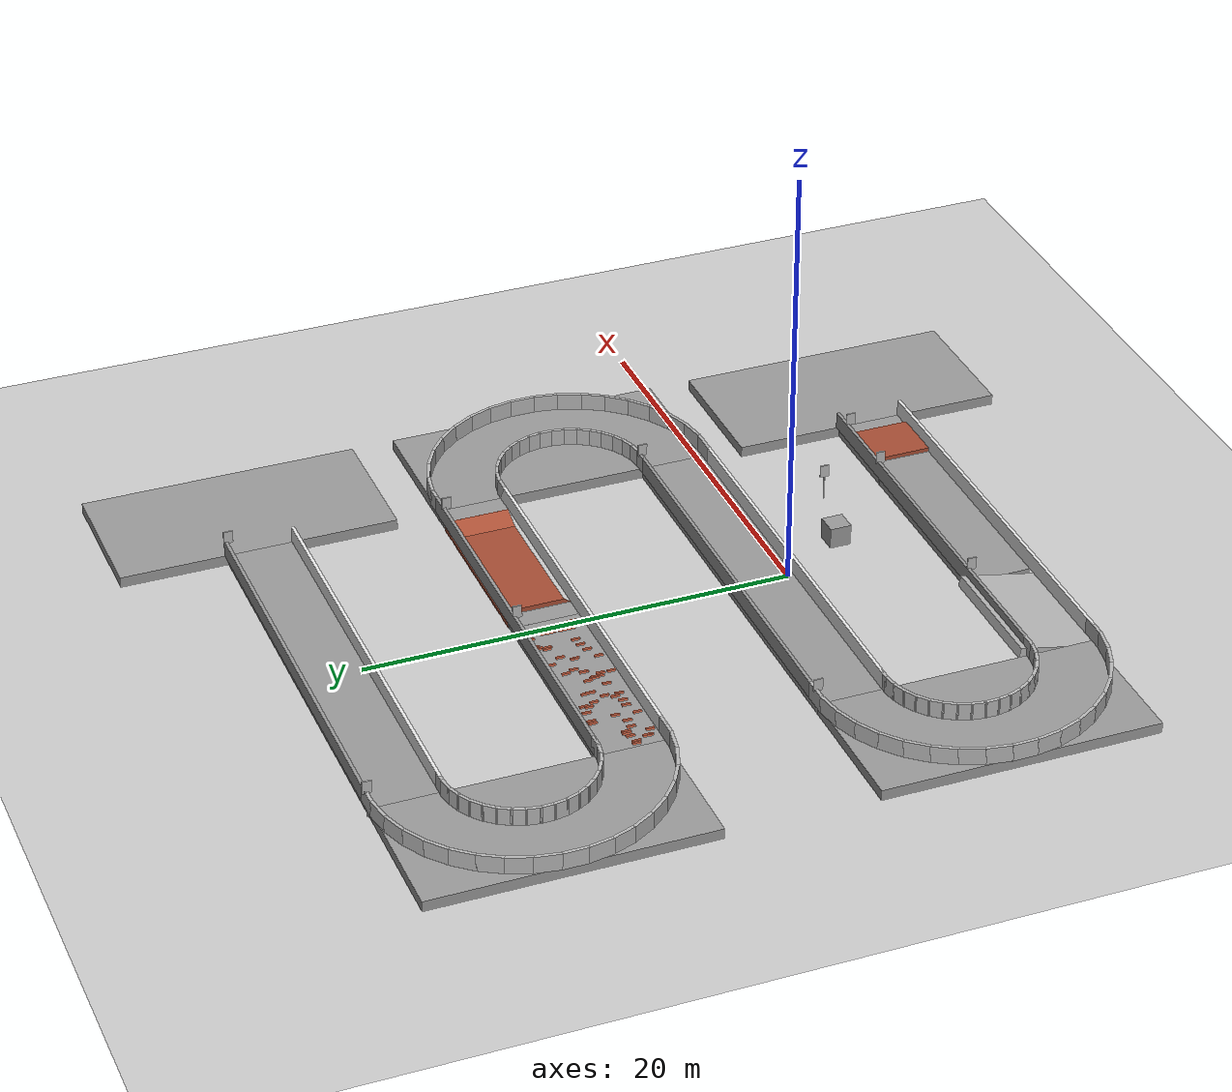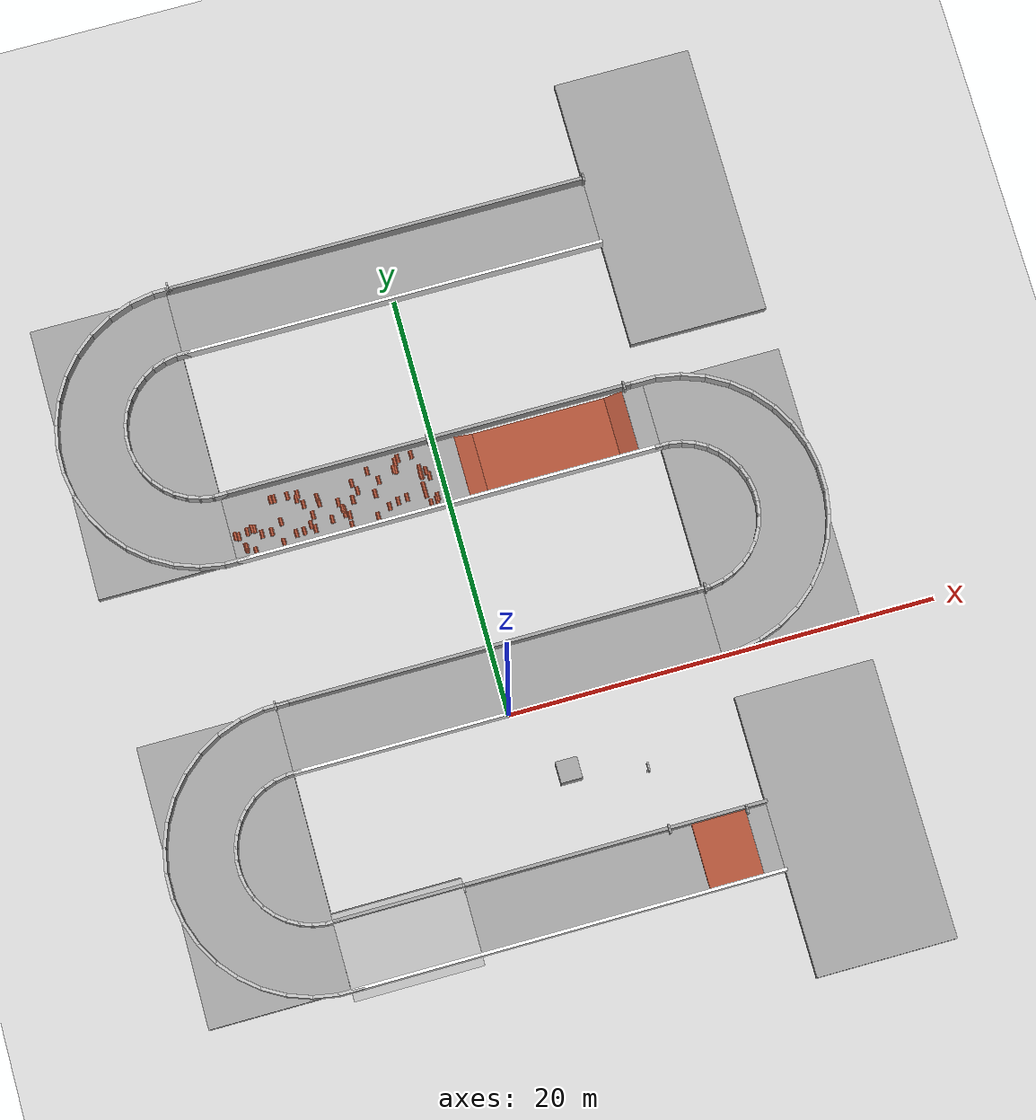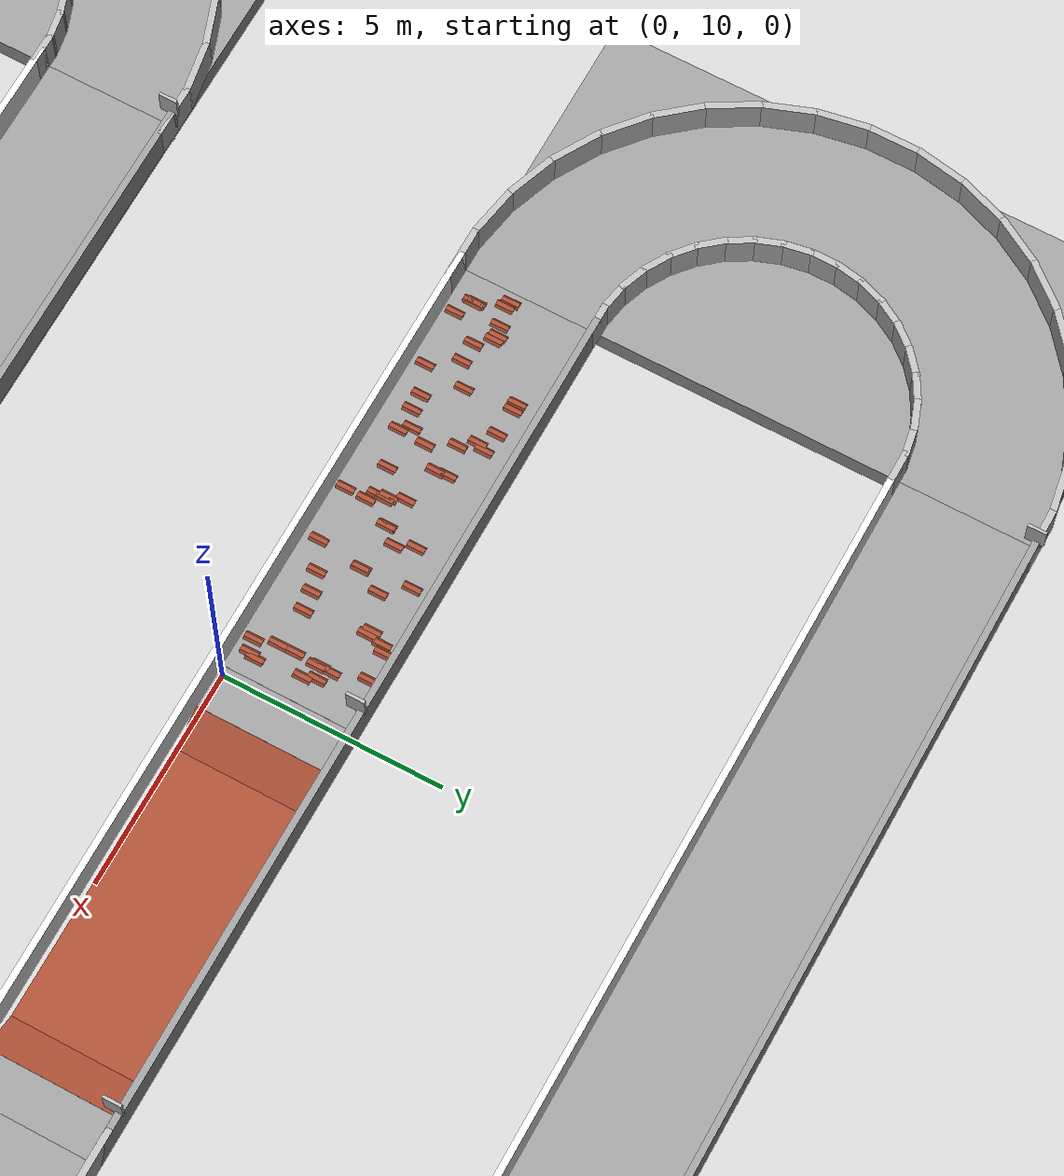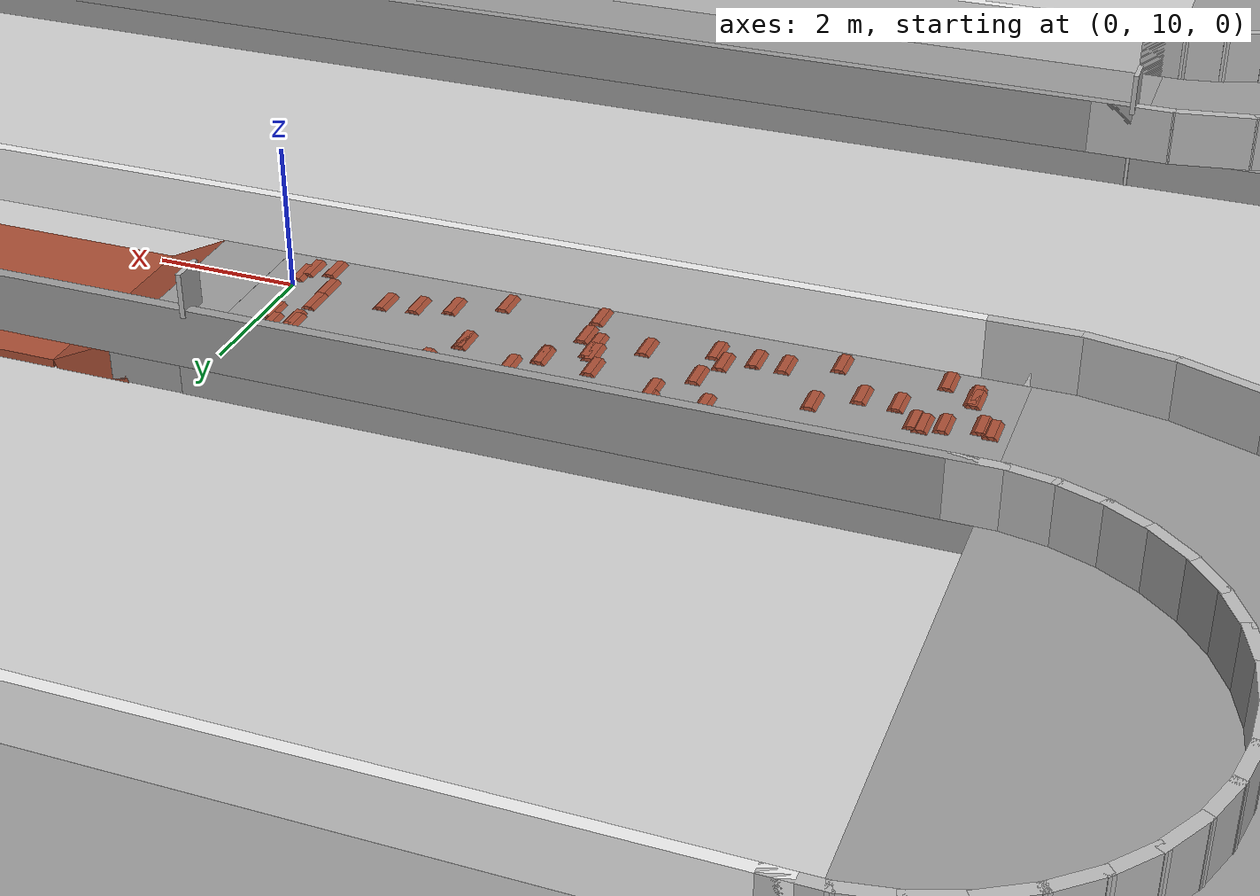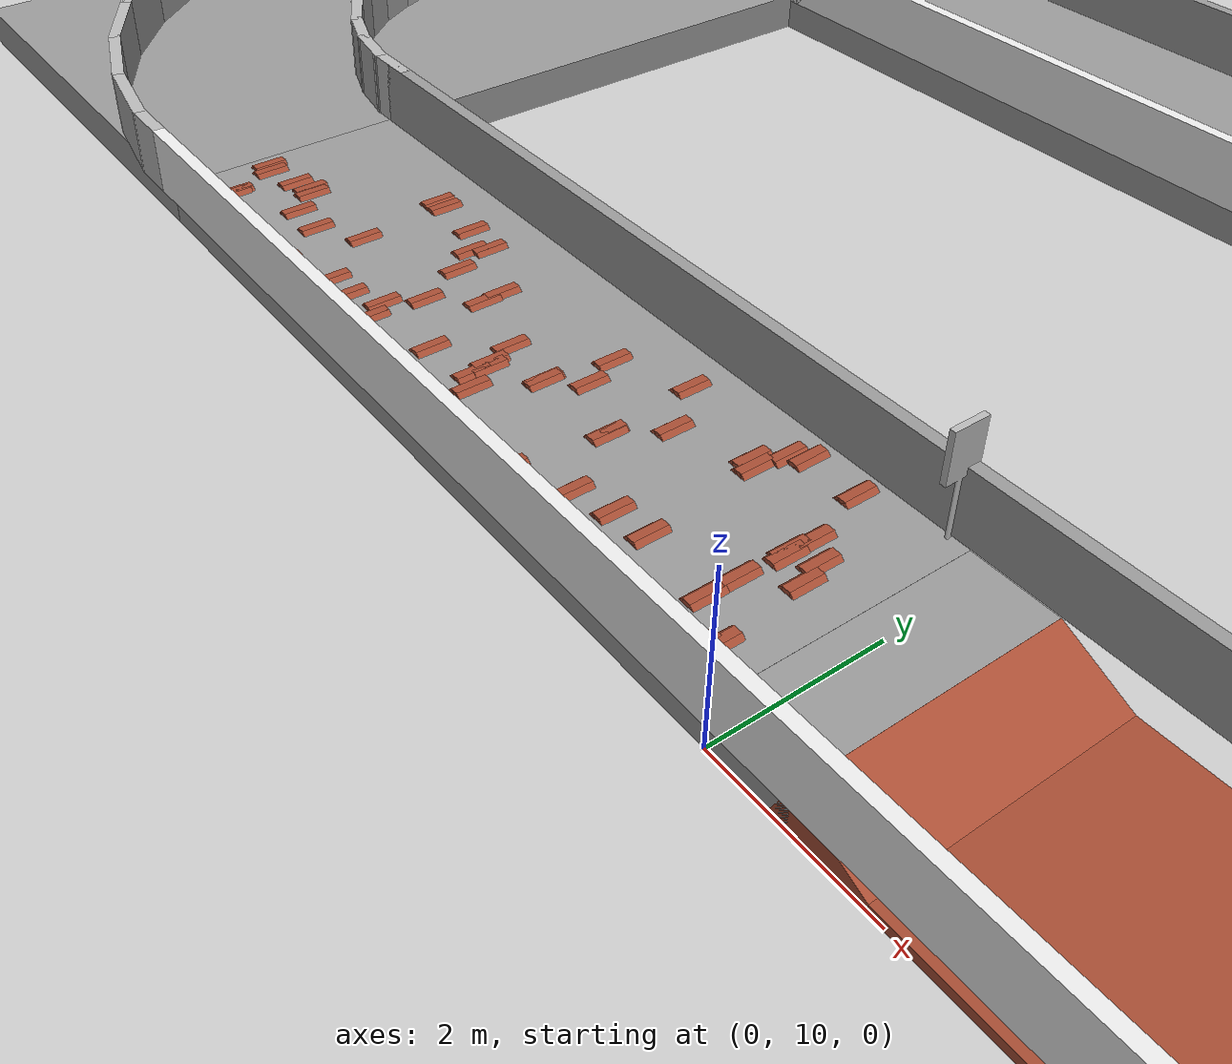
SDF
<sdf version="1.7">
 <world name="default">
  <light name="sun" type="directional">
   <pose>0 0 10 0 -0 0</pose>
   <diffuse>0.8 0.8 0.8 1</diffuse>
   <specular>0.2 0.2 0.2 1</specular>
   <attenuation>
    <range>1000</range>
    <constant>0.9</constant>
    <linear>0.01</linear>
    <quadratic>0.001</quadratic>
   </attenuation>
   <direction>-0.5 0.1 -0.9</direction>
   <spot><inner_angle>0</inner_angle><outer_angle>0</outer_angle><falloff>0</falloff></spot>
  </light>
  <model name="ground_plane">
   <static>1</static>
   <link name="link">
    <collision name="collision">
     <geometry><plane><normal>0 0 1</normal><size>100 100</size></plane></geometry>
     <surface><friction><ode><mu>100</mu><mu2>50</mu2></ode></friction></surface>
    </collision>
    <visual name="visual">
     <cast_shadows>0</cast_shadows>
     <geometry><plane><normal>0 0 1</normal><size>100 100</size></plane></geometry>
     <material>
      <script><uri>file://media/materials/scripts/gazebo.material</uri><name>Gazebo/Grey</name></script>
     </material>
    </visual>
   </link>
  </model>
  <gravity>0 0 -9.8</gravity>
  <magnetic_field>6e-06 2.3e-05 -4.2e-05</magnetic_field>
  <atmosphere type="adiabatic"/>
  <physics type="ode">
   <max_step_size>0.001</max_step_size>
   <real_time_factor>1</real_time_factor>
   <real_time_update_rate>1000</real_time_update_rate>
  </physics>
  <scene><ambient>0.4 0.4 0.4 1</ambient><background>0.7 0.7 0.7 1</background><shadows>1</shadows></scene>
  <audio><device>default</device></audio>
  <spherical_coordinates>
   <surface_model>EARTH_WGS84</surface_model>
   <latitude_deg>0</latitude_deg>
   <longitude_deg>0</longitude_deg>
   <elevation>0</elevation>
   <heading_deg>0</heading_deg>
  </spherical_coordinates>
  <model name="ika">
   <pose>0 -8.5 0.5 0 -0 0</pose>
   <static>1</static>
   <link name="Wall_1_0">
    <collision name="Wall_4_Collision">
     <geometry><box><size>20 0.15 0.8</size></box></geometry>
     <pose>0 0 0.4 0 -0 0</pose>
    </collision>
    <visual name="Wall_4_Visual">
     <pose>0 0 0.4 0 -0 0</pose>
     <geometry><box><size>20 0.15 0.8</size></box></geometry>
     <material>
      <script><uri>file://media/materials/scripts/gazebo.material</uri><name>Gazebo/Grey</name></script>
      <ambient>1 1 1 1</ambient>
     </material>
     <meta><layer>0</layer></meta>
    </visual>
    <pose>-0 1.575 0 0 -0 0</pose>
   </link>
   <link name="Wall_1_1">
    <collision name="Wall_7_Collision">
     <geometry><box><size>20 0.15 0.8</size></box></geometry>
     <pose>0 0 0.4 0 -0 0</pose>
    </collision>
    <visual name="Wall_7_Visual">
     <pose>0 0 0.4 0 -0 0</pose>
     <geometry><box><size>20 0.15 0.8</size></box></geometry>
     <material>
      <script><uri>file://media/materials/scripts/gazebo.material</uri><name>Gazebo/White</name></script>
      <ambient>1 1 1 1</ambient>
     </material>
     <meta><layer>0</layer></meta>
    </visual>
    <pose>-0 -1.575 0 0 -0 0</pose>
   </link>
   <link name="link_0">
    <pose>-10 11.575 0.4 0 -0 1.5708</pose>
    <collision name="col1"><geometry><box><size>0.15 1.2 0.8</size></box></geometry></collision>
    <visual name="vis1"><geometry><box><size>0.15 1.2 0.8</size></box></geometry></visual>
   </link>
   <link name="link_1">
    <pose>-11.1418 11.4751 0.4 0 -0 1.74533</pose>
    <collision name="col1"><geometry><box><size>0.15 1.2 0.8</size></box></geometry></collision>
    <visual name="vis1"><geometry><box><size>0.15 1.2 0.8</size></box></geometry></visual>
   </link>
   <link name="link_2">
    <pose>-12.2488 11.1785 0.4 0 -0 1.91987</pose>
    <collision name="col1"><geometry><box><size>0.15 1.2 0.8</size></box></geometry></collision>
    <visual name="vis1"><geometry><box><size>0.15 1.2 0.8</size></box></geometry></visual>
   </link>
   <link name="link_3">
    <pose>-13.2875 10.6941 0.4 0 -0 2.0944</pose>
    <collision name="col1"><geometry><box><size>0.15 1.2 0.8</size></box></geometry></collision>
    <visual name="vis1"><geometry><box><size>0.15 1.2 0.8</size></box></geometry></visual>
   </link>
   <link name="link_4">
    <pose>-14.2264 10.0367 0.4 0 -0 2.26893</pose>
    <collision name="col1"><geometry><box><size>0.15 1.2 0.8</size></box></geometry></collision>
    <visual name="vis1"><geometry><box><size>0.15 1.2 0.8</size></box></geometry></visual>
   </link>
   <link name="link_5">
    <pose>-15.0368 9.2263 0.4 0 -0 2.44347</pose>
    <collision name="col1"><geometry><box><size>0.15 1.2 0.8</size></box></geometry></collision>
    <visual name="vis1"><geometry><box><size>0.15 1.2 0.8</size></box></geometry></visual>
   </link>
   <link name="link_6">
    <pose>-15.6941 8.28746 0.4 0 -0 2.618</pose>
    <collision name="col1"><geometry><box><size>0.15 1.2 0.8</size></box></geometry></collision>
    <visual name="vis1"><geometry><box><size>0.15 1.2 0.8</size></box></geometry></visual>
   </link>
   <link name="link_7">
    <pose>-16.1785 7.24874 0.4 0 -0 2.79253</pose>
    <collision name="col1"><geometry><box><size>0.15 1.2 0.8</size></box></geometry></collision>
    <visual name="vis1"><geometry><box><size>0.15 1.2 0.8</size></box></geometry></visual>
   </link>
   <link name="link_8">
    <pose>-16.4751 6.14169 0.4 0 -0 2.96707</pose>
    <collision name="col1"><geometry><box><size>0.15 1.2 0.8</size></box></geometry></collision>
    <visual name="vis1"><geometry><box><size>0.15 1.2 0.8</size></box></geometry></visual>
   </link>
   <link name="link_9">
    <pose>-16.575 4.99995 0.4 0 -0 -3.14159</pose>
    <collision name="col1"><geometry><box><size>0.15 1.2 0.8</size></box></geometry></collision>
    <visual name="vis1"><geometry><box><size>0.15 1.2 0.8</size></box></geometry></visual>
   </link>
   <link name="link_10">
    <pose>-16.4751 3.85821 0.4 0 -0 -2.96705</pose>
    <collision name="col1"><geometry><box><size>0.15 1.2 0.8</size></box></geometry></collision>
    <visual name="vis1"><geometry><box><size>0.15 1.2 0.8</size></box></geometry></visual>
   </link>
   <link name="link_11">
    <pose>-16.1785 2.75117 0.4 0 -0 -2.79252</pose>
    <collision name="col1"><geometry><box><size>0.15 1.2 0.8</size></box></geometry></collision>
    <visual name="vis1"><geometry><box><size>0.15 1.2 0.8</size></box></geometry></visual>
   </link>
   <link name="link_12">
    <pose>-15.6941 1.71245 0.4 0 -0 -2.61799</pose>
    <collision name="col1"><geometry><box><size>0.15 1.2 0.8</size></box></geometry></collision>
    <visual name="vis1"><geometry><box><size>0.15 1.2 0.8</size></box></geometry></visual>
   </link>
   <link name="link_13">
    <pose>-15.0367 0.773626 0.4 0 -0 -2.44345</pose>
    <collision name="col1"><geometry><box><size>0.15 1.2 0.8</size></box></geometry></collision>
    <visual name="vis1"><geometry><box><size>0.15 1.2 0.8</size></box></geometry></visual>
   </link>
   <link name="link_14">
    <pose>-14.2263 -0.036782 0.4 0 -0 -2.26892</pose>
    <collision name="col1"><geometry><box><size>0.15 1.2 0.8</size></box></geometry></collision>
    <visual name="vis1"><geometry><box><size>0.15 1.2 0.8</size></box></geometry></visual>
   </link>
   <link name="link_15">
    <pose>-13.2874 -0.694149 0.4 0 -0 -2.09438</pose>
    <collision name="col1"><geometry><box><size>0.15 1.2 0.8</size></box></geometry></collision>
    <visual name="vis1"><geometry><box><size>0.15 1.2 0.8</size></box></geometry></visual>
   </link>
   <link name="link_16">
    <pose>-12.2487 -1.1785 0.4 0 -0 -1.91985</pose>
    <collision name="col1"><geometry><box><size>0.15 1.2 0.8</size></box></geometry></collision>
    <visual name="vis1"><geometry><box><size>0.15 1.2 0.8</size></box></geometry></visual>
   </link>
   <link name="link_17">
    <pose>-11.1417 -1.47512 0.4 0 -0 -1.74532</pose>
    <collision name="col1"><geometry><box><size>0.15 1.2 0.8</size></box></geometry></collision>
    <visual name="vis1"><geometry><box><size>0.15 1.2 0.8</size></box></geometry></visual>
   </link>
   <link name="link_18">
    <pose>-9.99993 -1.575 0.4 0 -0 -1.57079</pose>
    <collision name="col1"><geometry><box><size>0.15 1.2 0.8</size></box></geometry></collision>
    <visual name="vis1"><geometry><box><size>0.15 1.2 0.8</size></box></geometry></visual>
   </link>
   <link name="link_s1_0">
    <pose>-10 8.425 0.4 0 -0 1.5708</pose>
    <collision name="col1"><geometry><box><size>0.15 0.7 0.8</size></box></geometry></collision>
    <visual name="vis1"><geometry><box><size>0.15 0.7 0.8</size></box></geometry></visual>
   </link>
   <link name="link_s1_1">
    <pose>-10.5948 8.37296 0.4 0 -0 1.74533</pose>
    <collision name="col1"><geometry><box><size>0.15 0.7 0.8</size></box></geometry></collision>
    <visual name="vis1"><geometry><box><size>0.15 0.7 0.8</size></box></geometry></visual>
   </link>
   <link name="link_s1_2">
    <pose>-11.1714 8.21844 0.4 0 -0 1.91987</pose>
    <collision name="col1"><geometry><box><size>0.15 0.7 0.8</size></box></geometry></collision>
    <visual name="vis1"><geometry><box><size>0.15 0.7 0.8</size></box></geometry></visual>
   </link>
   <link name="link_s1_3">
    <pose>-11.7125 7.96613 0.4 0 -0 2.0944</pose>
    <collision name="col1"><geometry><box><size>0.15 0.7 0.8</size></box></geometry></collision>
    <visual name="vis1"><geometry><box><size>0.15 0.7 0.8</size></box></geometry></visual>
   </link>
   <link name="link_s1_4">
    <pose>-12.2016 7.62369 0.4 0 -0 2.26893</pose>
    <collision name="col1"><geometry><box><size>0.15 0.7 0.8</size></box></geometry></collision>
    <visual name="vis1"><geometry><box><size>0.15 0.7 0.8</size></box></geometry></visual>
   </link>
   <link name="link_s1_5">
    <pose>-12.6237 7.20153 0.4 0 -0 2.44347</pose>
    <collision name="col1"><geometry><box><size>0.15 0.7 0.8</size></box></geometry></collision>
    <visual name="vis1"><geometry><box><size>0.15 0.7 0.8</size></box></geometry></visual>
   </link>
   <link name="link_s1_6">
    <pose>-12.9661 6.71248 0.4 0 -0 2.618</pose>
    <collision name="col1"><geometry><box><size>0.15 0.7 0.8</size></box></geometry></collision>
    <visual name="vis1"><geometry><box><size>0.15 0.7 0.8</size></box></geometry></visual>
   </link>
   <link name="link_s1_7">
    <pose>-13.2185 6.1714 0.4 0 -0 2.79253</pose>
    <collision name="col1"><geometry><box><size>0.15 0.7 0.8</size></box></geometry></collision>
    <visual name="vis1"><geometry><box><size>0.15 0.7 0.8</size></box></geometry></visual>
   </link>
   <link name="link_s1_8">
    <pose>-13.373 5.59472 0.4 0 -0 2.96707</pose>
    <collision name="col1"><geometry><box><size>0.15 0.7 0.8</size></box></geometry></collision>
    <visual name="vis1"><geometry><box><size>0.15 0.7 0.8</size></box></geometry></visual>
   </link>
   <link name="link_s1_9">
    <pose>-13.425 4.99998 0.4 0 -0 -3.14159</pose>
    <collision name="col1"><geometry><box><size>0.15 0.7 0.8</size></box></geometry></collision>
    <visual name="vis1"><geometry><box><size>0.15 0.7 0.8</size></box></geometry></visual>
   </link>
   <link name="link_s1_10">
    <pose>-13.373 4.40523 0.4 0 -0 -2.96705</pose>
    <collision name="col1"><geometry><box><size>0.15 0.7 0.8</size></box></geometry></collision>
    <visual name="vis1"><geometry><box><size>0.15 0.7 0.8</size></box></geometry></visual>
   </link>
   <link name="link_s1_11">
    <pose>-13.2184 3.82856 0.4 0 -0 -2.79252</pose>
    <collision name="col1"><geometry><box><size>0.15 0.7 0.8</size></box></geometry></collision>
    <visual name="vis1"><geometry><box><size>0.15 0.7 0.8</size></box></geometry></visual>
   </link>
   <link name="link_s1_12">
    <pose>-12.9661 3.28748 0.4 0 -0 -2.61799</pose>
    <collision name="col1"><geometry><box><size>0.15 0.7 0.8</size></box></geometry></collision>
    <visual name="vis1"><geometry><box><size>0.15 0.7 0.8</size></box></geometry></visual>
   </link>
   <link name="link_s1_13">
    <pose>-12.6237 2.79843 0.4 0 -0 -2.44345</pose>
    <collision name="col1"><geometry><box><size>0.15 0.7 0.8</size></box></geometry></collision>
    <visual name="vis1"><geometry><box><size>0.15 0.7 0.8</size></box></geometry></visual>
   </link>
   <link name="link_s1_14">
    <pose>-12.2015 2.37628 0.4 0 -0 -2.26892</pose>
    <collision name="col1"><geometry><box><size>0.15 0.7 0.8</size></box></geometry></collision>
    <visual name="vis1"><geometry><box><size>0.15 0.7 0.8</size></box></geometry></visual>
   </link>
   <link name="link_s1_15">
    <pose>-11.7125 2.03385 0.4 0 -0 -2.09438</pose>
    <collision name="col1"><geometry><box><size>0.15 0.7 0.8</size></box></geometry></collision>
    <visual name="vis1"><geometry><box><size>0.15 0.7 0.8</size></box></geometry></visual>
   </link>
   <link name="link_s1_16">
    <pose>-11.1714 1.78154 0.4 0 -0 -1.91985</pose>
    <collision name="col1"><geometry><box><size>0.15 0.7 0.8</size></box></geometry></collision>
    <visual name="vis1"><geometry><box><size>0.15 0.7 0.8</size></box></geometry></visual>
   </link>
   <link name="link_s1_17">
    <pose>-10.5947 1.62703 0.4 0 -0 -1.74532</pose>
    <collision name="col1"><geometry><box><size>0.15 0.7 0.8</size></box></geometry></collision>
    <visual name="vis1"><geometry><box><size>0.15 0.7 0.8</size></box></geometry></visual>
   </link>
   <link name="link_s1_18">
    <pose>-9.99996 1.575 0.4 0 -0 -1.57079</pose>
    <collision name="col1"><geometry><box><size>0.15 0.7 0.8</size></box></geometry></collision>
    <visual name="vis1"><geometry><box><size>0.15 0.7 0.8</size></box></geometry></visual>
   </link>
   <link name="Wall_2_0">
    <pose>-0 11.575 0 0 -0 0</pose>
    <collision name="Wall_4_Collision">
     <geometry><box><size>20 0.15 0.8</size></box></geometry>
     <pose>0 0 0.4 0 -0 0</pose>
    </collision>
    <visual name="Wall_4_Visual">
     <pose>0 0 0.4 0 -0 0</pose>
     <geometry><box><size>20 0.15 0.8</size></box></geometry>
     <material>
      <script><uri>file://media/materials/scripts/gazebo.material</uri><name>Gazebo/Grey</name></script>
      <ambient>1 1 1 1</ambient>
     </material>
     <meta><layer>0</layer></meta>
    </visual>
   </link>
   <link name="Wall_2_1">
    <pose>-0 8.425 0 0 -0 0</pose>
    <collision name="Wall_7_Collision">
     <geometry><box><size>20 0.15 0.8</size></box></geometry>
     <pose>0 0 0.4 0 -0 0</pose>
    </collision>
    <visual name="Wall_7_Visual">
     <pose>0 0 0.4 0 -0 0</pose>
     <geometry><box><size>20 0.15 0.8</size></box></geometry>
     <material>
      <script><uri>file://media/materials/scripts/gazebo.material</uri><name>Gazebo/White</name></script>
      <ambient>1 1 1 1</ambient>
     </material>
     <meta><layer>0</layer></meta>
    </visual>
   </link>
   <link name="link_s2_0">
    <pose>9.99999 11.575 0.4 0 0 -1.5708</pose>
    <collision name="col1"><geometry><box><size>0.15 0.7 0.8</size></box></geometry></collision>
    <visual name="vis1"><geometry><box><size>0.15 0.7 0.8</size></box></geometry></visual>
   </link>
   <link name="link_s2_1">
    <pose>10.5947 11.627 0.4 0 0 -1.39627</pose>
    <collision name="col1"><geometry><box><size>0.15 0.7 0.8</size></box></geometry></collision>
    <visual name="vis1"><geometry><box><size>0.15 0.7 0.8</size></box></geometry></visual>
   </link>
   <link name="link_s2_2">
    <pose>11.1714 11.7815 0.4 0 0 -1.22173</pose>
    <collision name="col1"><geometry><box><size>0.15 0.7 0.8</size></box></geometry></collision>
    <visual name="vis1"><geometry><box><size>0.15 0.7 0.8</size></box></geometry></visual>
   </link>
   <link name="link_s2_3">
    <pose>11.7125 12.0339 0.4 0 0 -1.0472</pose>
    <collision name="col1"><geometry><box><size>0.15 0.7 0.8</size></box></geometry></collision>
    <visual name="vis1"><geometry><box><size>0.15 0.7 0.8</size></box></geometry></visual>
   </link>
   <link name="link_s2_4">
    <pose>12.2015 12.3763 0.4 0 0 -0.872667</pose>
    <collision name="col1"><geometry><box><size>0.15 0.7 0.8</size></box></geometry></collision>
    <visual name="vis1"><geometry><box><size>0.15 0.7 0.8</size></box></geometry></visual>
   </link>
   <link name="link_s2_5">
    <pose>12.6237 12.7984 0.4 0 0 -0.698133</pose>
    <collision name="col1"><geometry><box><size>0.15 0.7 0.8</size></box></geometry></collision>
    <visual name="vis1"><geometry><box><size>0.15 0.7 0.8</size></box></geometry></visual>
   </link>
   <link name="link_s2_6">
    <pose>12.9661 13.2875 0.4 0 0 -0.5236</pose>
    <collision name="col1"><geometry><box><size>0.15 0.7 0.8</size></box></geometry></collision>
    <visual name="vis1"><geometry><box><size>0.15 0.7 0.8</size></box></geometry></visual>
   </link>
   <link name="link_s2_7">
    <pose>13.2184 13.8286 0.4 0 0 -0.349067</pose>
    <collision name="col1"><geometry><box><size>0.15 0.7 0.8</size></box></geometry></collision>
    <visual name="vis1"><geometry><box><size>0.15 0.7 0.8</size></box></geometry></visual>
   </link>
   <link name="link_s2_8">
    <pose>13.373 14.4053 0.4 0 0 -0.174533</pose>
    <collision name="col1"><geometry><box><size>0.15 0.7 0.8</size></box></geometry></collision>
    <visual name="vis1"><geometry><box><size>0.15 0.7 0.8</size></box></geometry></visual>
   </link>
   <link name="link_s2_9">
    <pose>13.425 15 0.4 0 -0 0</pose>
    <collision name="col1"><geometry><box><size>0.15 0.7 0.8</size></box></geometry></collision>
    <visual name="vis1"><geometry><box><size>0.15 0.7 0.8</size></box></geometry></visual>
   </link>
   <link name="link_s2_10">
    <pose>13.373 15.5947 0.4 0 -0 0.174533</pose>
    <collision name="col1"><geometry><box><size>0.15 0.7 0.8</size></box></geometry></collision>
    <visual name="vis1"><geometry><box><size>0.15 0.7 0.8</size></box></geometry></visual>
   </link>
   <link name="link_s2_11">
    <pose>13.2184 16.1714 0.4 0 -0 0.349067</pose>
    <collision name="col1"><geometry><box><size>0.15 0.7 0.8</size></box></geometry></collision>
    <visual name="vis1"><geometry><box><size>0.15 0.7 0.8</size></box></geometry></visual>
   </link>
   <link name="link_s2_12">
    <pose>12.9661 16.7125 0.4 0 -0 0.5236</pose>
    <collision name="col1"><geometry><box><size>0.15 0.7 0.8</size></box></geometry></collision>
    <visual name="vis1"><geometry><box><size>0.15 0.7 0.8</size></box></geometry></visual>
   </link>
   <link name="link_s2_13">
    <pose>12.6237 17.2016 0.4 0 -0 0.698133</pose>
    <collision name="col1"><geometry><box><size>0.15 0.7 0.8</size></box></geometry></collision>
    <visual name="vis1"><geometry><box><size>0.15 0.7 0.8</size></box></geometry></visual>
   </link>
   <link name="link_s2_14">
    <pose>12.2015 17.6237 0.4 0 -0 0.872667</pose>
    <collision name="col1"><geometry><box><size>0.15 0.7 0.8</size></box></geometry></collision>
    <visual name="vis1"><geometry><box><size>0.15 0.7 0.8</size></box></geometry></visual>
   </link>
   <link name="link_s2_15">
    <pose>11.7125 17.9661 0.4 0 -0 1.0472</pose>
    <collision name="col1"><geometry><box><size>0.15 0.7 0.8</size></box></geometry></collision>
    <visual name="vis1"><geometry><box><size>0.15 0.7 0.8</size></box></geometry></visual>
   </link>
   <link name="link_s2_16">
    <pose>11.1714 18.2185 0.4 0 -0 1.22173</pose>
    <collision name="col1"><geometry><box><size>0.15 0.7 0.8</size></box></geometry></collision>
    <visual name="vis1"><geometry><box><size>0.15 0.7 0.8</size></box></geometry></visual>
   </link>
   <link name="link_s2_17">
    <pose>10.5947 18.373 0.4 0 -0 1.39627</pose>
    <collision name="col1"><geometry><box><size>0.15 0.7 0.8</size></box></geometry></collision>
    <visual name="vis1"><geometry><box><size>0.15 0.7 0.8</size></box></geometry></visual>
   </link>
   <link name="link_s2_18">
    <pose>9.99999 18.425 0.4 0 -0 1.5708</pose>
    <collision name="col1"><geometry><box><size>0.15 0.7 0.8</size></box></geometry></collision>
    <visual name="vis1"><geometry><box><size>0.15 0.7 0.8</size></box></geometry></visual>
   </link>
   <link name="link_l2_0">
    <pose>9.99998 8.425 0.4 0 0 -1.5708</pose>
    <collision name="col1"><geometry><box><size>0.15 1.2 0.8</size></box></geometry></collision>
    <visual name="vis1"><geometry><box><size>0.15 1.2 0.8</size></box></geometry></visual>
   </link>
   <link name="link_l2_1">
    <pose>11.1417 8.52488 0.4 0 0 -1.39627</pose>
    <collision name="col1"><geometry><box><size>0.15 1.2 0.8</size></box></geometry></collision>
    <visual name="vis1"><geometry><box><size>0.15 1.2 0.8</size></box></geometry></visual>
   </link>
   <link name="link_l2_2">
    <pose>12.2488 8.82151 0.4 0 0 -1.22173</pose>
    <collision name="col1"><geometry><box><size>0.15 1.2 0.8</size></box></geometry></collision>
    <visual name="vis1"><geometry><box><size>0.15 1.2 0.8</size></box></geometry></visual>
   </link>
   <link name="link_l2_3">
    <pose>13.2875 9.30588 0.4 0 0 -1.0472</pose>
    <collision name="col1"><geometry><box><size>0.15 1.2 0.8</size></box></geometry></collision>
    <visual name="vis1"><geometry><box><size>0.15 1.2 0.8</size></box></geometry></visual>
   </link>
   <link name="link_l2_4">
    <pose>14.2263 9.96325 0.4 0 0 -0.872667</pose>
    <collision name="col1"><geometry><box><size>0.15 1.2 0.8</size></box></geometry></collision>
    <visual name="vis1"><geometry><box><size>0.15 1.2 0.8</size></box></geometry></visual>
   </link>
   <link name="link_l2_5">
    <pose>15.0367 10.7737 0.4 0 0 -0.698133</pose>
    <collision name="col1"><geometry><box><size>0.15 1.2 0.8</size></box></geometry></collision>
    <visual name="vis1"><geometry><box><size>0.15 1.2 0.8</size></box></geometry></visual>
   </link>
   <link name="link_l2_6">
    <pose>15.6941 11.7125 0.4 0 0 -0.5236</pose>
    <collision name="col1"><geometry><box><size>0.15 1.2 0.8</size></box></geometry></collision>
    <visual name="vis1"><geometry><box><size>0.15 1.2 0.8</size></box></geometry></visual>
   </link>
   <link name="link_l2_7">
    <pose>16.1785 12.7512 0.4 0 0 -0.349067</pose>
    <collision name="col1"><geometry><box><size>0.15 1.2 0.8</size></box></geometry></collision>
    <visual name="vis1"><geometry><box><size>0.15 1.2 0.8</size></box></geometry></visual>
   </link>
   <link name="link_l2_8">
    <pose>16.4751 13.8583 0.4 0 0 -0.174533</pose>
    <collision name="col1"><geometry><box><size>0.15 1.2 0.8</size></box></geometry></collision>
    <visual name="vis1"><geometry><box><size>0.15 1.2 0.8</size></box></geometry></visual>
   </link>
   <link name="link_l2_9">
    <pose>16.575 15 0.4 0 -0 0</pose>
    <collision name="col1"><geometry><box><size>0.15 1.2 0.8</size></box></geometry></collision>
    <visual name="vis1"><geometry><box><size>0.15 1.2 0.8</size></box></geometry></visual>
   </link>
   <link name="link_l2_10">
    <pose>16.4751 16.1417 0.4 0 -0 0.174533</pose>
    <collision name="col1"><geometry><box><size>0.15 1.2 0.8</size></box></geometry></collision>
    <visual name="vis1"><geometry><box><size>0.15 1.2 0.8</size></box></geometry></visual>
   </link>
   <link name="link_l2_11">
    <pose>16.1785 17.2488 0.4 0 -0 0.349067</pose>
    <collision name="col1"><geometry><box><size>0.15 1.2 0.8</size></box></geometry></collision>
    <visual name="vis1"><geometry><box><size>0.15 1.2 0.8</size></box></geometry></visual>
   </link>
   <link name="link_l2_12">
    <pose>15.6941 18.2875 0.4 0 -0 0.5236</pose>
    <collision name="col1"><geometry><box><size>0.15 1.2 0.8</size></box></geometry></collision>
    <visual name="vis1"><geometry><box><size>0.15 1.2 0.8</size></box></geometry></visual>
   </link>
   <link name="link_l2_13">
    <pose>15.0367 19.2263 0.4 0 -0 0.698133</pose>
    <collision name="col1"><geometry><box><size>0.15 1.2 0.8</size></box></geometry></collision>
    <visual name="vis1"><geometry><box><size>0.15 1.2 0.8</size></box></geometry></visual>
   </link>
   <link name="link_l2_14">
    <pose>14.2263 20.0368 0.4 0 -0 0.872667</pose>
    <collision name="col1"><geometry><box><size>0.15 1.2 0.8</size></box></geometry></collision>
    <visual name="vis1"><geometry><box><size>0.15 1.2 0.8</size></box></geometry></visual>
   </link>
   <link name="link_l2_15">
    <pose>13.2875 20.6941 0.4 0 -0 1.0472</pose>
    <collision name="col1"><geometry><box><size>0.15 1.2 0.8</size></box></geometry></collision>
    <visual name="vis1"><geometry><box><size>0.15 1.2 0.8</size></box></geometry></visual>
   </link>
   <link name="link_l2_16">
    <pose>12.2488 21.1785 0.4 0 -0 1.22173</pose>
    <collision name="col1"><geometry><box><size>0.15 1.2 0.8</size></box></geometry></collision>
    <visual name="vis1"><geometry><box><size>0.15 1.2 0.8</size></box></geometry></visual>
   </link>
   <link name="link_l2_17">
    <pose>11.1417 21.4751 0.4 0 -0 1.39627</pose>
    <collision name="col1"><geometry><box><size>0.15 1.2 0.8</size></box></geometry></collision>
    <visual name="vis1"><geometry><box><size>0.15 1.2 0.8</size></box></geometry></visual>
   </link>
   <link name="link_l2_18">
    <pose>9.99998 21.575 0.4 0 -0 1.5708</pose>
    <collision name="col1"><geometry><box><size>0.15 1.2 0.8</size></box></geometry></collision>
    <visual name="vis1"><geometry><box><size>0.15 1.2 0.8</size></box></geometry></visual>
   </link>
   <link name="Wall_3_0">
    <pose>-0 21.575 0 0 -0 0</pose>
    <collision name="Wall_4_Collision">
     <geometry><box><size>20 0.15 0.8</size></box></geometry>
     <pose>0 0 0.4 0 -0 0</pose>
    </collision>
    <visual name="Wall_4_Visual">
     <pose>0 0 0.4 0 -0 0</pose>
     <geometry><box><size>20 0.15 0.8</size></box></geometry>
     <material>
      <script><uri>file://media/materials/scripts/gazebo.material</uri><name>Gazebo/Grey</name></script>
      <ambient>1 1 1 1</ambient>
     </material>
     <meta><layer>0</layer></meta>
    </visual>
   </link>
   <link name="Wall_3_1">
    <pose>-0 18.425 0 0 -0 0</pose>
    <collision name="Wall_7_Collision">
     <geometry><box><size>20 0.15 0.8</size></box></geometry>
     <pose>0 0 0.4 0 -0 0</pose>
    </collision>
    <visual name="Wall_7_Visual">
     <pose>0 0 0.4 0 -0 0</pose>
     <geometry><box><size>20 0.15 0.8</size></box></geometry>
     <material>
      <script><uri>file://media/materials/scripts/gazebo.material</uri><name>Gazebo/White</name></script>
      <ambient>1 1 1 1</ambient>
     </material>
     <meta><layer>0</layer></meta>
    </visual>
   </link>
   <link name="link_l3_0">
    <pose>-10 31.575 0.4 0 -0 1.5708</pose>
    <collision name="col1"><geometry><box><size>0.15 1.2 0.8</size></box></geometry></collision>
    <visual name="vis1"><geometry><box><size>0.15 1.2 0.8</size></box></geometry></visual>
   </link>
   <link name="link_l3_1">
    <pose>-11.1418 31.4751 0.4 0 -0 1.74533</pose>
    <collision name="col1"><geometry><box><size>0.15 1.2 0.8</size></box></geometry></collision>
    <visual name="vis1"><geometry><box><size>0.15 1.2 0.8</size></box></geometry></visual>
   </link>
   <link name="link_l3_2">
    <pose>-12.2488 31.1785 0.4 0 -0 1.91987</pose>
    <collision name="col1"><geometry><box><size>0.15 1.2 0.8</size></box></geometry></collision>
    <visual name="vis1"><geometry><box><size>0.15 1.2 0.8</size></box></geometry></visual>
   </link>
   <link name="link_l3_3">
    <pose>-13.2875 30.6941 0.4 0 -0 2.0944</pose>
    <collision name="col1"><geometry><box><size>0.15 1.2 0.8</size></box></geometry></collision>
    <visual name="vis1"><geometry><box><size>0.15 1.2 0.8</size></box></geometry></visual>
   </link>
   <link name="link_l3_4">
    <pose>-14.2264 30.0367 0.4 0 -0 2.26893</pose>
    <collision name="col1"><geometry><box><size>0.15 1.2 0.8</size></box></geometry></collision>
    <visual name="vis1"><geometry><box><size>0.15 1.2 0.8</size></box></geometry></visual>
   </link>
   <link name="link_l3_5">
    <pose>-15.0368 29.2263 0.4 0 -0 2.44347</pose>
    <collision name="col1"><geometry><box><size>0.15 1.2 0.8</size></box></geometry></collision>
    <visual name="vis1"><geometry><box><size>0.15 1.2 0.8</size></box></geometry></visual>
   </link>
   <link name="link_l3_6">
    <pose>-15.6941 28.2875 0.4 0 -0 2.618</pose>
    <collision name="col1"><geometry><box><size>0.15 1.2 0.8</size></box></geometry></collision>
    <visual name="vis1"><geometry><box><size>0.15 1.2 0.8</size></box></geometry></visual>
   </link>
   <link name="link_l3_7">
    <pose>-16.1785 27.2487 0.4 0 -0 2.79253</pose>
    <collision name="col1"><geometry><box><size>0.15 1.2 0.8</size></box></geometry></collision>
    <visual name="vis1"><geometry><box><size>0.15 1.2 0.8</size></box></geometry></visual>
   </link>
   <link name="link_l3_8">
    <pose>-16.4751 26.1417 0.4 0 -0 2.96707</pose>
    <collision name="col1"><geometry><box><size>0.15 1.2 0.8</size></box></geometry></collision>
    <visual name="vis1"><geometry><box><size>0.15 1.2 0.8</size></box></geometry></visual>
   </link>
   <link name="link_l3_9">
    <pose>-16.575 25 0.4 0 -0 -3.14159</pose>
    <collision name="col1"><geometry><box><size>0.15 1.2 0.8</size></box></geometry></collision>
    <visual name="vis1"><geometry><box><size>0.15 1.2 0.8</size></box></geometry></visual>
   </link>
   <link name="link_l3_10">
    <pose>-16.4751 23.8582 0.4 0 -0 -2.96705</pose>
    <collision name="col1"><geometry><box><size>0.15 1.2 0.8</size></box></geometry></collision>
    <visual name="vis1"><geometry><box><size>0.15 1.2 0.8</size></box></geometry></visual>
   </link>
   <link name="link_l3_11">
    <pose>-16.1785 22.7512 0.4 0 -0 -2.79252</pose>
    <collision name="col1"><geometry><box><size>0.15 1.2 0.8</size></box></geometry></collision>
    <visual name="vis1"><geometry><box><size>0.15 1.2 0.8</size></box></geometry></visual>
   </link>
   <link name="link_l3_12">
    <pose>-15.6941 21.7125 0.4 0 -0 -2.61799</pose>
    <collision name="col1"><geometry><box><size>0.15 1.2 0.8</size></box></geometry></collision>
    <visual name="vis1"><geometry><box><size>0.15 1.2 0.8</size></box></geometry></visual>
   </link>
   <link name="link_l3_13">
    <pose>-15.0367 20.7736 0.4 0 -0 -2.44345</pose>
    <collision name="col1"><geometry><box><size>0.15 1.2 0.8</size></box></geometry></collision>
    <visual name="vis1"><geometry><box><size>0.15 1.2 0.8</size></box></geometry></visual>
   </link>
   <link name="link_l3_14">
    <pose>-14.2263 19.9632 0.4 0 -0 -2.26892</pose>
    <collision name="col1"><geometry><box><size>0.15 1.2 0.8</size></box></geometry></collision>
    <visual name="vis1"><geometry><box><size>0.15 1.2 0.8</size></box></geometry></visual>
   </link>
   <link name="link_l3_15">
    <pose>-13.2874 19.3059 0.4 0 -0 -2.09438</pose>
    <collision name="col1"><geometry><box><size>0.15 1.2 0.8</size></box></geometry></collision>
    <visual name="vis1"><geometry><box><size>0.15 1.2 0.8</size></box></geometry></visual>
   </link>
   <link name="link_l3_16">
    <pose>-12.2487 18.8215 0.4 0 -0 -1.91985</pose>
    <collision name="col1"><geometry><box><size>0.15 1.2 0.8</size></box></geometry></collision>
    <visual name="vis1"><geometry><box><size>0.15 1.2 0.8</size></box></geometry></visual>
   </link>
   <link name="link_l3_17">
    <pose>-11.1417 18.5249 0.4 0 -0 -1.74532</pose>
    <collision name="col1"><geometry><box><size>0.15 1.2 0.8</size></box></geometry></collision>
    <visual name="vis1"><geometry><box><size>0.15 1.2 0.8</size></box></geometry></visual>
   </link>
   <link name="link_l3_18">
    <pose>-9.99993 18.425 0.4 0 -0 -1.57079</pose>
    <collision name="col1"><geometry><box><size>0.15 1.2 0.8</size></box></geometry></collision>
    <visual name="vis1"><geometry><box><size>0.15 1.2 0.8</size></box></geometry></visual>
   </link>
   <link name="link_s3_0">
    <pose>-10 28.425 0.4 0 -0 1.5708</pose>
    <collision name="col1"><geometry><box><size>0.15 0.7 0.8</size></box></geometry></collision>
    <visual name="vis1"><geometry><box><size>0.15 0.7 0.8</size></box></geometry></visual>
   </link>
   <link name="link_s3_1">
    <pose>-10.5948 28.373 0.4 0 -0 1.74533</pose>
    <collision name="col1"><geometry><box><size>0.15 0.7 0.8</size></box></geometry></collision>
    <visual name="vis1"><geometry><box><size>0.15 0.7 0.8</size></box></geometry></visual>
   </link>
   <link name="link_s3_2">
    <pose>-11.1714 28.2184 0.4 0 -0 1.91987</pose>
    <collision name="col1"><geometry><box><size>0.15 0.7 0.8</size></box></geometry></collision>
    <visual name="vis1"><geometry><box><size>0.15 0.7 0.8</size></box></geometry></visual>
   </link>
   <link name="link_s3_3">
    <pose>-11.7125 27.9661 0.4 0 -0 2.0944</pose>
    <collision name="col1"><geometry><box><size>0.15 0.7 0.8</size></box></geometry></collision>
    <visual name="vis1"><geometry><box><size>0.15 0.7 0.8</size></box></geometry></visual>
   </link>
   <link name="link_s3_4">
    <pose>-12.2016 27.6237 0.4 0 -0 2.26893</pose>
    <collision name="col1"><geometry><box><size>0.15 0.7 0.8</size></box></geometry></collision>
    <visual name="vis1"><geometry><box><size>0.15 0.7 0.8</size></box></geometry></visual>
   </link>
   <link name="link_s3_5">
    <pose>-12.6237 27.2015 0.4 0 -0 2.44347</pose>
    <collision name="col1"><geometry><box><size>0.15 0.7 0.8</size></box></geometry></collision>
    <visual name="vis1"><geometry><box><size>0.15 0.7 0.8</size></box></geometry></visual>
   </link>
   <link name="link_s3_6">
    <pose>-12.9661 26.7125 0.4 0 -0 2.618</pose>
    <collision name="col1"><geometry><box><size>0.15 0.7 0.8</size></box></geometry></collision>
    <visual name="vis1"><geometry><box><size>0.15 0.7 0.8</size></box></geometry></visual>
   </link>
   <link name="link_s3_7">
    <pose>-13.2185 26.1714 0.4 0 -0 2.79253</pose>
    <collision name="col1"><geometry><box><size>0.15 0.7 0.8</size></box></geometry></collision>
    <visual name="vis1"><geometry><box><size>0.15 0.7 0.8</size></box></geometry></visual>
   </link>
   <link name="link_s3_8">
    <pose>-13.373 25.5947 0.4 0 -0 2.96707</pose>
    <collision name="col1"><geometry><box><size>0.15 0.7 0.8</size></box></geometry></collision>
    <visual name="vis1"><geometry><box><size>0.15 0.7 0.8</size></box></geometry></visual>
   </link>
   <link name="link_s3_9">
    <pose>-13.425 25 0.4 0 -0 -3.14159</pose>
    <collision name="col1"><geometry><box><size>0.15 0.7 0.8</size></box></geometry></collision>
    <visual name="vis1"><geometry><box><size>0.15 0.7 0.8</size></box></geometry></visual>
   </link>
   <link name="link_s3_10">
    <pose>-13.373 24.4052 0.4 0 -0 -2.96705</pose>
    <collision name="col1"><geometry><box><size>0.15 0.7 0.8</size></box></geometry></collision>
    <visual name="vis1"><geometry><box><size>0.15 0.7 0.8</size></box></geometry></visual>
   </link>
   <link name="link_s3_11">
    <pose>-13.2184 23.8286 0.4 0 -0 -2.79252</pose>
    <collision name="col1"><geometry><box><size>0.15 0.7 0.8</size></box></geometry></collision>
    <visual name="vis1"><geometry><box><size>0.15 0.7 0.8</size></box></geometry></visual>
   </link>
   <link name="link_s3_12">
    <pose>-12.9661 23.2875 0.4 0 -0 -2.61799</pose>
    <collision name="col1"><geometry><box><size>0.15 0.7 0.8</size></box></geometry></collision>
    <visual name="vis1"><geometry><box><size>0.15 0.7 0.8</size></box></geometry></visual>
   </link>
   <link name="link_s3_13">
    <pose>-12.6237 22.7984 0.4 0 -0 -2.44345</pose>
    <collision name="col1"><geometry><box><size>0.15 0.7 0.8</size></box></geometry></collision>
    <visual name="vis1"><geometry><box><size>0.15 0.7 0.8</size></box></geometry></visual>
   </link>
   <link name="link_s3_14">
    <pose>-12.2015 22.3763 0.4 0 -0 -2.26892</pose>
    <collision name="col1"><geometry><box><size>0.15 0.7 0.8</size></box></geometry></collision>
    <visual name="vis1"><geometry><box><size>0.15 0.7 0.8</size></box></geometry></visual>
   </link>
   <link name="link_s3_15">
    <pose>-11.7125 22.0338 0.4 0 -0 -2.09438</pose>
    <collision name="col1"><geometry><box><size>0.15 0.7 0.8</size></box></geometry></collision>
    <visual name="vis1"><geometry><box><size>0.15 0.7 0.8</size></box></geometry></visual>
   </link>
   <link name="link_s3_16">
    <pose>-11.1714 21.7815 0.4 0 -0 -1.91985</pose>
    <collision name="col1"><geometry><box><size>0.15 0.7 0.8</size></box></geometry></collision>
    <visual name="vis1"><geometry><box><size>0.15 0.7 0.8</size></box></geometry></visual>
   </link>
   <link name="link_s3_17">
    <pose>-10.5947 21.627 0.4 0 -0 -1.74532</pose>
    <collision name="col1"><geometry><box><size>0.15 0.7 0.8</size></box></geometry></collision>
    <visual name="vis1"><geometry><box><size>0.15 0.7 0.8</size></box></geometry></visual>
   </link>
   <link name="link_s3_18">
    <pose>-9.99996 21.575 0.4 0 -0 -1.57079</pose>
    <collision name="col1"><geometry><box><size>0.15 0.7 0.8</size></box></geometry></collision>
    <visual name="vis1"><geometry><box><size>0.15 0.7 0.8</size></box></geometry></visual>
   </link>
   <link name="Wall_4_0">
    <pose>0 31.575 0 0 -0 0</pose>
    <collision name="Wall_4_Collision">
     <geometry><box><size>20 0.15 0.8</size></box></geometry>
     <pose>0 0 0.4 0 -0 0</pose>
    </collision>
    <visual name="Wall_4_Visual">
     <pose>0 0 0.4 0 -0 0</pose>
     <geometry><box><size>20 0.15 0.8</size></box></geometry>
     <material>
      <script><uri>file://media/materials/scripts/gazebo.material</uri><name>Gazebo/Grey</name></script>
      <ambient>1 1 1 1</ambient>
     </material>
     <meta><layer>0</layer></meta>
    </visual>
   </link>
   <link name="Wall_4_1">
    <pose>-0 28.425 0 0 -0 0</pose>
    <collision name="Wall_7_Collision">
     <geometry><box><size>20 0.15 0.8</size></box></geometry>
     <pose>0 0 0.4 0 -0 0</pose>
    </collision>
    <visual name="Wall_7_Visual">
     <pose>0 0 0.4 0 -0 0</pose>
     <geometry><box><size>20 0.15 0.8</size></box></geometry>
     <material>
      <script><uri>file://media/materials/scripts/gazebo.material</uri><name>Gazebo/White</name></script>
      <ambient>1 1 1 1</ambient>
     </material>
     <meta><layer>0</layer></meta>
    </visual>
   </link>
  </model>
  <model name="ika2">
   <pose>-0.027776 1.5013 0 0 -0 0</pose>
   <static>1</static>
   <link name="straight_2">
    <collision name="main_ground_Collision">
     <geometry><box><size>20 3 0.5</size></box></geometry>
     <pose>0 0 0.25 0 -0 0</pose>
    </collision>
    <visual name="main_ground_Visual">
     <pose>0 0 0.25 0 -0 0</pose>
     <geometry><box><size>20 3 0.5</size></box></geometry>
     <material>
      <script><uri>file://media/materials/scripts/gazebo.material</uri><name>Gazebo/Grey</name></script>
      <ambient>1 1 1 1</ambient>
     </material>
     <meta><layer>0</layer></meta>
    </visual>
   </link>
   <link name="straight_3">
    <pose>-5 10 0 0 -0 0</pose>
    <collision name="main_ground_Collision">
     <geometry><box><size>10 3 0.5</size></box></geometry>
     <pose>0 0 0.25 0 -0 0</pose>
    </collision>
    <visual name="main_ground_Visual">
     <pose>0 0 0.25 0 -0 0</pose>
     <geometry><box><size>10 3 0.5</size></box></geometry>
     <material>
      <script><uri>file://media/materials/scripts/gazebo.material</uri><name>Gazebo/Grey</name></script>
      <ambient>1 1 1 1</ambient>
     </material>
     <meta><layer>0</layer></meta>
    </visual>
   </link>
   <link name="straight_4">
    <pose>0 20 0 0 -0 0</pose>
    <collision name="main_ground_Collision">
     <geometry><box><size>20 3 0.5</size></box></geometry>
     <pose>0 0 0.25 0 -0 0</pose>
    </collision>
    <visual name="main_ground_Visual">
     <pose>0 0 0.25 0 -0 0</pose>
     <geometry><box><size>20 3 0.5</size></box></geometry>
     <material>
      <script><uri>file://media/materials/scripts/gazebo.material</uri><name>Gazebo/Grey</name></script>
      <ambient>1 1 1 1</ambient>
     </material>
     <meta><layer>0</layer></meta>
    </visual>
   </link>
   <link name="round_1">
    <pose>-10 -5 0 0 -0 0</pose>
    <collision name="main_ground_Collision">
     <geometry><box><size>6.5 13 0.5</size></box></geometry>
     <pose>-3.25 0 0.25 0 -0 0</pose>
    </collision>
    <visual name="main_ground_Visual">
     <pose>-3.25 0 0.25 0 -0 0</pose>
     <geometry><box><size>6.5 13 0.5</size></box></geometry>
     <material>
      <script><uri>file://media/materials/scripts/gazebo.material</uri><name>Gazebo/Grey</name></script>
      <ambient>1 1 1 1</ambient>
     </material>
     <meta><layer>0</layer></meta>
    </visual>
   </link>
   <link name="round_2">
    <pose>16.5 5 0 0 -0 0</pose>
    <collision name="main_ground_Collision">
     <geometry><box><size>6.5 13 0.5</size></box></geometry>
     <pose>-3.25 0 0.25 0 -0 0</pose>
    </collision>
    <visual name="main_ground_Visual">
     <pose>-3.25 0 0.25 0 -0 0</pose>
     <geometry><box><size>6.5 13 0.5</size></box></geometry>
     <material>
      <script><uri>file://media/materials/scripts/gazebo.material</uri><name>Gazebo/Grey</name></script>
      <ambient>1 1 1 1</ambient>
     </material>
     <meta><layer>0</layer></meta>
    </visual>
   </link>
   <link name="round_3">
    <pose>-10 15 0 0 -0 0</pose>
    <collision name="main_ground_Collision">
     <geometry><box><size>6.5 13 0.5</size></box></geometry>
     <pose>-3.25 0 0.25 0 -0 0</pose>
    </collision>
    <visual name="main_ground_Visual">
     <pose>-3.25 0 0.25 0 -0 0</pose>
     <geometry><box><size>6.5 13 0.5</size></box></geometry>
     <material>
      <script><uri>file://media/materials/scripts/gazebo.material</uri><name>Gazebo/Grey</name></script>
      <ambient>1 1 1 1</ambient>
     </material>
     <meta><layer>0</layer></meta>
    </visual>
   </link>
   <link name="final">
    <pose>16.5 20 0 0 -0 0</pose>
    <collision name="main_ground_Collision">
     <geometry><box><size>6.5 13 0.5</size></box></geometry>
     <pose>-3.25 0 0.25 0 -0 0</pose>
    </collision>
    <visual name="main_ground_Visual">
     <pose>-3.25 0 0.25 0 -0 0</pose>
     <geometry><box><size>6.5 13 0.5</size></box></geometry>
     <material>
      <script><uri>file://media/materials/scripts/gazebo.material</uri><name>Gazebo/Grey</name></script>
      <ambient>1 1 1 1</ambient>
     </material>
     <meta><layer>0</layer></meta>
    </visual>
   </link>
   <link name="start">
    <pose>16.5 -10 0 0 -0 0</pose>
    <collision name="main_ground_Collision">
     <geometry><box><size>6.5 13 0.5</size></box></geometry>
     <pose>-3.25 0 0.25 0 -0 0</pose>
    </collision>
    <visual name="main_ground_Visual">
     <pose>-3.25 0 0.25 0 -0 0</pose>
     <geometry><box><size>6.5 13 0.5</size></box></geometry>
     <material>
      <script><uri>file://media/materials/scripts/gazebo.material</uri><name>Gazebo/Grey</name></script>
      <ambient>1 1 1 1</ambient>
     </material>
     <meta><layer>0</layer></meta>
    </visual>
   </link>
   <link name="straight_1_1">
    <pose>3 -10 0 0 -0 0</pose>
    <collision name="main_ground_Collision">
     <geometry><box><size>14 3 0.5</size></box></geometry>
     <pose>0 0 0.25 0 -0 0</pose>
    </collision>
    <visual name="main_ground_Visual">
     <pose>0 0 0.25 0 -0 0</pose>
     <geometry><box><size>14 3 0.5</size></box></geometry>
     <material>
      <script><uri>file://media/materials/scripts/gazebo.material</uri><name>Gazebo/Grey</name></script>
      <ambient>1 1 1 1</ambient>
     </material>
     <meta><layer>0</layer></meta>
    </visual>
   </link>
   <link name="yan">
    <pose>-7 -10 0.3 0.197 -0 0</pose>
    <collision name="main_ground_Collision"><geometry><box><size>6 4 0.5</size></box></geometry></collision>
    <visual name="main_ground_Visual">
     <geometry><box><size>6 4 0.5</size></box></geometry>
     <meta><layer>0</layer></meta>
    </visual>
   </link>
  </model>
  <model name="dik">
   <pose>7.75 -8.5 0.5 0 -0 0</pose>
   <static>1</static>
   <link name="dik">
    <collision name="dik_Collision">
     <geometry><box><size>2.5 3 0.2</size></box></geometry>
     <pose>0 0 0.1 0 -0 0</pose>
    </collision>
    <visual name="dik_Visual">
     <pose>0 0 0.1 0 -0 0</pose>
     <geometry><box><size>2.5 3 0.2</size></box></geometry>
     <material>
      <script><uri>file://media/materials/scripts/gazebo.material</uri><name>Gazebo/Bricks</name></script>
      <ambient>1 1 1 1</ambient>
     </material>
     <meta><layer>0</layer></meta>
    </visual>
   </link>
  </model>
  <model name="tumsek">
   <static>1</static>
   <pose>-5.17447 11.4027 0.5 0 -0 0</pose>
   <link name="tumsek_main_0">
    <pose>0.442808 -0.537221 0 0 -0 0</pose>
    <collision name="tumsek_Collision">
     <geometry><box><size>0.1 0.4 0.05</size></box></geometry>
     <pose>0 0 0.025 0 -0 0</pose>
    </collision>
    <visual name="tumsek_Visual">
     <pose>0 0 0.025 0 -0 0</pose>
     <geometry><box><size>0.1 0.4 0.05</size></box></geometry>
     <material>
      <script><uri>file://media/materials/scripts/gazebo.material</uri><name>Gazebo/Bricks</name></script>
      <ambient>1 1 1 1</ambient>
     </material>
     <meta><layer>0</layer></meta>
    </visual>
   </link>
   <link name="tumsek_front_0">
    <pose>0.492808 -0.537221 0 0 0.785 0</pose>
    <collision name="tumsek_Collision"><geometry><box><size>0.0707 0.4 0.0707</size></box></geometry></collision>
    <visual name="tumsek_Visual">
     <geometry><box><size>0.0707 0.4 0.0707</size></box></geometry>
     <material>
      <script><uri>file://media/materials/scripts/gazebo.material</uri><name>Gazebo/Bricks</name></script>
      <ambient>1 1 1 1</ambient>
     </material>
    </visual>
   </link>
   <link name="tumsek_back_0">
    <pose>0.392808 -0.537221 0 0 0.785 0</pose>
    <collision name="tumsek_Collision"><geometry><box><size>0.0707 0.4 0.0707</size></box></geometry></collision>
    <visual name="tumsek_Visual">
     <geometry><box><size>0.0707 0.4 0.0707</size></box></geometry>
     <material>
      <script><uri>file://media/materials/scripts/gazebo.material</uri><name>Gazebo/Bricks</name></script>
      <ambient>1 1 1 1</ambient>
     </material>
    </visual>
   </link>
   <link name="tumsek_main_1">
    <pose>-0.18536 -0.64129 0 0 -0 0</pose>
    <collision name="tumsek_Collision">
     <geometry><box><size>0.1 0.4 0.05</size></box></geometry>
     <pose>0 0 0.025 0 -0 0</pose>
    </collision>
    <visual name="tumsek_Visual">
     <pose>0 0 0.025 0 -0 0</pose>
     <geometry><box><size>0.1 0.4 0.05</size></box></geometry>
     <material>
      <script><uri>file://media/materials/scripts/gazebo.material</uri><name>Gazebo/Bricks</name></script>
      <ambient>1 1 1 1</ambient>
     </material>
     <meta><layer>0</layer></meta>
    </visual>
   </link>
   <link name="tumsek_front_1">
    <pose>-0.13536 -0.64129 0 0 0.785 0</pose>
    <collision name="tumsek_Collision"><geometry><box><size>0.0707 0.4 0.0707</size></box></geometry></collision>
    <visual name="tumsek_Visual">
     <geometry><box><size>0.0707 0.4 0.0707</size></box></geometry>
     <material>
      <script><uri>file://media/materials/scripts/gazebo.material</uri><name>Gazebo/Bricks</name></script>
      <ambient>1 1 1 1</ambient>
     </material>
    </visual>
   </link>
   <link name="tumsek_back_1">
    <pose>-0.23536 -0.64129 0 0 0.785 0</pose>
    <collision name="tumsek_Collision"><geometry><box><size>0.0707 0.4 0.0707</size></box></geometry></collision>
    <visual name="tumsek_Visual">
     <geometry><box><size>0.0707 0.4 0.0707</size></box></geometry>
     <material>
      <script><uri>file://media/materials/scripts/gazebo.material</uri><name>Gazebo/Bricks</name></script>
      <ambient>1 1 1 1</ambient>
     </material>
    </visual>
   </link>
   <link name="tumsek_main_2">
    <pose>-0.578517 0.253678 0 0 -0 0</pose>
    <collision name="tumsek_Collision">
     <geometry><box><size>0.1 0.4 0.05</size></box></geometry>
     <pose>0 0 0.025 0 -0 0</pose>
    </collision>
    <visual name="tumsek_Visual">
     <pose>0 0 0.025 0 -0 0</pose>
     <geometry><box><size>0.1 0.4 0.05</size></box></geometry>
     <material>
      <script><uri>file://media/materials/scripts/gazebo.material</uri><name>Gazebo/Bricks</name></script>
      <ambient>1 1 1 1</ambient>
     </material>
     <meta><layer>0</layer></meta>
    </visual>
   </link>
   <link name="tumsek_front_2">
    <pose>-0.528517 0.253678 0 0 0.785 0</pose>
    <collision name="tumsek_Collision"><geometry><box><size>0.0707 0.4 0.0707</size></box></geometry></collision>
    <visual name="tumsek_Visual">
     <geometry><box><size>0.0707 0.4 0.0707</size></box></geometry>
     <material>
      <script><uri>file://media/materials/scripts/gazebo.material</uri><name>Gazebo/Bricks</name></script>
      <ambient>1 1 1 1</ambient>
     </material>
    </visual>
   </link>
   <link name="tumsek_back_2">
    <pose>-0.628517 0.253678 0 0 0.785 0</pose>
    <collision name="tumsek_Collision"><geometry><box><size>0.0707 0.4 0.0707</size></box></geometry></collision>
    <visual name="tumsek_Visual">
     <geometry><box><size>0.0707 0.4 0.0707</size></box></geometry>
     <material>
      <script><uri>file://media/materials/scripts/gazebo.material</uri><name>Gazebo/Bricks</name></script>
      <ambient>1 1 1 1</ambient>
     </material>
    </visual>
   </link>
   <link name="tumsek_main_3">
    <pose>-2.98653 -0.469523 0 0 -0 0</pose>
    <collision name="tumsek_Collision">
     <geometry><box><size>0.1 0.4 0.05</size></box></geometry>
     <pose>0 0 0.025 0 -0 0</pose>
    </collision>
    <visual name="tumsek_Visual">
     <pose>0 0 0.025 0 -0 0</pose>
     <geometry><box><size>0.1 0.4 0.05</size></box></geometry>
     <material>
      <script><uri>file://media/materials/scripts/gazebo.material</uri><name>Gazebo/Bricks</name></script>
      <ambient>1 1 1 1</ambient>
     </material>
     <meta><layer>0</layer></meta>
    </visual>
   </link>
   <link name="tumsek_front_3">
    <pose>-2.93654 -0.469523 0 0 0.785 0</pose>
    <collision name="tumsek_Collision"><geometry><box><size>0.0707 0.4 0.0707</size></box></geometry></collision>
    <visual name="tumsek_Visual">
     <geometry><box><size>0.0707 0.4 0.0707</size></box></geometry>
     <material>
      <script><uri>file://media/materials/scripts/gazebo.material</uri><name>Gazebo/Bricks</name></script>
      <ambient>1 1 1 1</ambient>
     </material>
    </visual>
   </link>
   <link name="tumsek_back_3">
    <pose>-3.03654 -0.469523 0 0 0.785 0</pose>
    <collision name="tumsek_Collision"><geometry><box><size>0.0707 0.4 0.0707</size></box></geometry></collision>
    <visual name="tumsek_Visual">
     <geometry><box><size>0.0707 0.4 0.0707</size></box></geometry>
     <material>
      <script><uri>file://media/materials/scripts/gazebo.material</uri><name>Gazebo/Bricks</name></script>
      <ambient>1 1 1 1</ambient>
     </material>
    </visual>
   </link>
   <link name="tumsek_main_4">
    <pose>-0.987853 -0.219527 0 0 -0 0</pose>
    <collision name="tumsek_Collision">
     <geometry><box><size>0.1 0.4 0.05</size></box></geometry>
     <pose>0 0 0.025 0 -0 0</pose>
    </collision>
    <visual name="tumsek_Visual">
     <pose>0 0 0.025 0 -0 0</pose>
     <geometry><box><size>0.1 0.4 0.05</size></box></geometry>
     <material>
      <script><uri>file://media/materials/scripts/gazebo.material</uri><name>Gazebo/Bricks</name></script>
      <ambient>1 1 1 1</ambient>
     </material>
     <meta><layer>0</layer></meta>
    </visual>
   </link>
   <link name="tumsek_front_4">
    <pose>-0.937853 -0.219527 0 0 0.785 0</pose>
    <collision name="tumsek_Collision"><geometry><box><size>0.0707 0.4 0.0707</size></box></geometry></collision>
    <visual name="tumsek_Visual">
     <geometry><box><size>0.0707 0.4 0.0707</size></box></geometry>
     <material>
      <script><uri>file://media/materials/scripts/gazebo.material</uri><name>Gazebo/Bricks</name></script>
      <ambient>1 1 1 1</ambient>
     </material>
    </visual>
   </link>
   <link name="tumsek_back_4">
    <pose>-1.03785 -0.219527 0 0 0.785 0</pose>
    <collision name="tumsek_Collision"><geometry><box><size>0.0707 0.4 0.0707</size></box></geometry></collision>
    <visual name="tumsek_Visual">
     <geometry><box><size>0.0707 0.4 0.0707</size></box></geometry>
     <material>
      <script><uri>file://media/materials/scripts/gazebo.material</uri><name>Gazebo/Bricks</name></script>
      <ambient>1 1 1 1</ambient>
     </material>
    </visual>
   </link>
   <link name="tumsek_main_5">
    <pose>4.60433 0.123551 0 0 -0 0</pose>
    <collision name="tumsek_Collision">
     <geometry><box><size>0.1 0.4 0.05</size></box></geometry>
     <pose>0 0 0.025 0 -0 0</pose>
    </collision>
    <visual name="tumsek_Visual">
     <pose>0 0 0.025 0 -0 0</pose>
     <geometry><box><size>0.1 0.4 0.05</size></box></geometry>
     <material>
      <script><uri>file://media/materials/scripts/gazebo.material</uri><name>Gazebo/Bricks</name></script>
      <ambient>1 1 1 1</ambient>
     </material>
     <meta><layer>0</layer></meta>
    </visual>
   </link>
   <link name="tumsek_front_5">
    <pose>4.65433 0.123551 0 0 0.785 0</pose>
    <collision name="tumsek_Collision"><geometry><box><size>0.0707 0.4 0.0707</size></box></geometry></collision>
    <visual name="tumsek_Visual">
     <geometry><box><size>0.0707 0.4 0.0707</size></box></geometry>
     <material>
      <script><uri>file://media/materials/scripts/gazebo.material</uri><name>Gazebo/Bricks</name></script>
      <ambient>1 1 1 1</ambient>
     </material>
    </visual>
   </link>
   <link name="tumsek_back_5">
    <pose>4.55433 0.123551 0 0 0.785 0</pose>
    <collision name="tumsek_Collision"><geometry><box><size>0.0707 0.4 0.0707</size></box></geometry></collision>
    <visual name="tumsek_Visual">
     <geometry><box><size>0.0707 0.4 0.0707</size></box></geometry>
     <material>
      <script><uri>file://media/materials/scripts/gazebo.material</uri><name>Gazebo/Bricks</name></script>
      <ambient>1 1 1 1</ambient>
     </material>
    </visual>
   </link>
   <link name="tumsek_main_6">
    <pose>2.92633 -0.629082 0 0 -0 0</pose>
    <collision name="tumsek_Collision">
     <geometry><box><size>0.1 0.4 0.05</size></box></geometry>
     <pose>0 0 0.025 0 -0 0</pose>
    </collision>
    <visual name="tumsek_Visual">
     <pose>0 0 0.025 0 -0 0</pose>
     <geometry><box><size>0.1 0.4 0.05</size></box></geometry>
     <material>
      <script><uri>file://media/materials/scripts/gazebo.material</uri><name>Gazebo/Bricks</name></script>
      <ambient>1 1 1 1</ambient>
     </material>
     <meta><layer>0</layer></meta>
    </visual>
   </link>
   <link name="tumsek_front_6">
    <pose>2.97633 -0.629082 0 0 0.785 0</pose>
    <collision name="tumsek_Collision"><geometry><box><size>0.0707 0.4 0.0707</size></box></geometry></collision>
    <visual name="tumsek_Visual">
     <geometry><box><size>0.0707 0.4 0.0707</size></box></geometry>
     <material>
      <script><uri>file://media/materials/scripts/gazebo.material</uri><name>Gazebo/Bricks</name></script>
      <ambient>1 1 1 1</ambient>
     </material>
    </visual>
   </link>
   <link name="tumsek_back_6">
    <pose>2.87633 -0.629082 0 0 0.785 0</pose>
    <collision name="tumsek_Collision"><geometry><box><size>0.0707 0.4 0.0707</size></box></geometry></collision>
    <visual name="tumsek_Visual">
     <geometry><box><size>0.0707 0.4 0.0707</size></box></geometry>
     <material>
      <script><uri>file://media/materials/scripts/gazebo.material</uri><name>Gazebo/Bricks</name></script>
      <ambient>1 1 1 1</ambient>
     </material>
    </visual>
   </link>
   <link name="tumsek_main_7">
    <pose>1.08805 0.739805 0 0 -0 0</pose>
    <collision name="tumsek_Collision">
     <geometry><box><size>0.1 0.4 0.05</size></box></geometry>
     <pose>0 0 0.025 0 -0 0</pose>
    </collision>
    <visual name="tumsek_Visual">
     <pose>0 0 0.025 0 -0 0</pose>
     <geometry><box><size>0.1 0.4 0.05</size></box></geometry>
     <material>
      <script><uri>file://media/materials/scripts/gazebo.material</uri><name>Gazebo/Bricks</name></script>
      <ambient>1 1 1 1</ambient>
     </material>
     <meta><layer>0</layer></meta>
    </visual>
   </link>
   <link name="tumsek_front_7">
    <pose>1.13805 0.739805 0 0 0.785 0</pose>
    <collision name="tumsek_Collision"><geometry><box><size>0.0707 0.4 0.0707</size></box></geometry></collision>
    <visual name="tumsek_Visual">
     <geometry><box><size>0.0707 0.4 0.0707</size></box></geometry>
     <material>
      <script><uri>file://media/materials/scripts/gazebo.material</uri><name>Gazebo/Bricks</name></script>
      <ambient>1 1 1 1</ambient>
     </material>
    </visual>
   </link>
   <link name="tumsek_back_7">
    <pose>1.03805 0.739805 0 0 0.785 0</pose>
    <collision name="tumsek_Collision"><geometry><box><size>0.0707 0.4 0.0707</size></box></geometry></collision>
    <visual name="tumsek_Visual">
     <geometry><box><size>0.0707 0.4 0.0707</size></box></geometry>
     <material>
      <script><uri>file://media/materials/scripts/gazebo.material</uri><name>Gazebo/Bricks</name></script>
      <ambient>1 1 1 1</ambient>
     </material>
    </visual>
   </link>
   <link name="tumsek_main_8">
    <pose>3.2512 1.16803 0 0 -0 0</pose>
    <collision name="tumsek_Collision">
     <geometry><box><size>0.1 0.4 0.05</size></box></geometry>
     <pose>0 0 0.025 0 -0 0</pose>
    </collision>
    <visual name="tumsek_Visual">
     <pose>0 0 0.025 0 -0 0</pose>
     <geometry><box><size>0.1 0.4 0.05</size></box></geometry>
     <material>
      <script><uri>file://media/materials/scripts/gazebo.material</uri><name>Gazebo/Bricks</name></script>
      <ambient>1 1 1 1</ambient>
     </material>
     <meta><layer>0</layer></meta>
    </visual>
   </link>
   <link name="tumsek_front_8">
    <pose>3.3012 1.16803 0 0 0.785 0</pose>
    <collision name="tumsek_Collision"><geometry><box><size>0.0707 0.4 0.0707</size></box></geometry></collision>
    <visual name="tumsek_Visual">
     <geometry><box><size>0.0707 0.4 0.0707</size></box></geometry>
     <material>
      <script><uri>file://media/materials/scripts/gazebo.material</uri><name>Gazebo/Bricks</name></script>
      <ambient>1 1 1 1</ambient>
     </material>
    </visual>
   </link>
   <link name="tumsek_back_8">
    <pose>3.2012 1.16803 0 0 0.785 0</pose>
    <collision name="tumsek_Collision"><geometry><box><size>0.0707 0.4 0.0707</size></box></geometry></collision>
    <visual name="tumsek_Visual">
     <geometry><box><size>0.0707 0.4 0.0707</size></box></geometry>
     <material>
      <script><uri>file://media/materials/scripts/gazebo.material</uri><name>Gazebo/Bricks</name></script>
      <ambient>1 1 1 1</ambient>
     </material>
    </visual>
   </link>
   <link name="tumsek_main_9">
    <pose>-2.67469 0.983993 0 0 -0 0</pose>
    <collision name="tumsek_Collision">
     <geometry><box><size>0.1 0.4 0.05</size></box></geometry>
     <pose>0 0 0.025 0 -0 0</pose>
    </collision>
    <visual name="tumsek_Visual">
     <pose>0 0 0.025 0 -0 0</pose>
     <geometry><box><size>0.1 0.4 0.05</size></box></geometry>
     <material>
      <script><uri>file://media/materials/scripts/gazebo.material</uri><name>Gazebo/Bricks</name></script>
      <ambient>1 1 1 1</ambient>
     </material>
     <meta><layer>0</layer></meta>
    </visual>
   </link>
   <link name="tumsek_front_9">
    <pose>-2.62469 0.983993 0 0 0.785 0</pose>
    <collision name="tumsek_Collision"><geometry><box><size>0.0707 0.4 0.0707</size></box></geometry></collision>
    <visual name="tumsek_Visual">
     <geometry><box><size>0.0707 0.4 0.0707</size></box></geometry>
     <material>
      <script><uri>file://media/materials/scripts/gazebo.material</uri><name>Gazebo/Bricks</name></script>
      <ambient>1 1 1 1</ambient>
     </material>
    </visual>
   </link>
   <link name="tumsek_back_9">
    <pose>-2.72469 0.983993 0 0 0.785 0</pose>
    <collision name="tumsek_Collision"><geometry><box><size>0.0707 0.4 0.0707</size></box></geometry></collision>
    <visual name="tumsek_Visual">
     <geometry><box><size>0.0707 0.4 0.0707</size></box></geometry>
     <material>
      <script><uri>file://media/materials/scripts/gazebo.material</uri><name>Gazebo/Bricks</name></script>
      <ambient>1 1 1 1</ambient>
     </material>
    </visual>
   </link>
   <link name="tumsek_main_10">
    <pose>0.618424 -1.15214 0 0 -0 0</pose>
    <collision name="tumsek_Collision">
     <geometry><box><size>0.1 0.4 0.05</size></box></geometry>
     <pose>0 0 0.025 0 -0 0</pose>
    </collision>
    <visual name="tumsek_Visual">
     <pose>0 0 0.025 0 -0 0</pose>
     <geometry><box><size>0.1 0.4 0.05</size></box></geometry>
     <material>
      <script><uri>file://media/materials/scripts/gazebo.material</uri><name>Gazebo/Bricks</name></script>
      <ambient>1 1 1 1</ambient>
     </material>
     <meta><layer>0</layer></meta>
    </visual>
   </link>
   <link name="tumsek_front_10">
    <pose>0.668424 -1.15214 0 0 0.785 0</pose>
    <collision name="tumsek_Collision"><geometry><box><size>0.0707 0.4 0.0707</size></box></geometry></collision>
    <visual name="tumsek_Visual">
     <geometry><box><size>0.0707 0.4 0.0707</size></box></geometry>
     <material>
      <script><uri>file://media/materials/scripts/gazebo.material</uri><name>Gazebo/Bricks</name></script>
      <ambient>1 1 1 1</ambient>
     </material>
    </visual>
   </link>
   <link name="tumsek_back_10">
    <pose>0.568424 -1.15214 0 0 0.785 0</pose>
    <collision name="tumsek_Collision"><geometry><box><size>0.0707 0.4 0.0707</size></box></geometry></collision>
    <visual name="tumsek_Visual">
     <geometry><box><size>0.0707 0.4 0.0707</size></box></geometry>
     <material>
      <script><uri>file://media/materials/scripts/gazebo.material</uri><name>Gazebo/Bricks</name></script>
      <ambient>1 1 1 1</ambient>
     </material>
    </visual>
   </link>
   <link name="tumsek_main_11">
    <pose>2.31423 0.549426 0 0 -0 0</pose>
    <collision name="tumsek_Collision">
     <geometry><box><size>0.1 0.4 0.05</size></box></geometry>
     <pose>0 0 0.025 0 -0 0</pose>
    </collision>
    <visual name="tumsek_Visual">
     <pose>0 0 0.025 0 -0 0</pose>
     <geometry><box><size>0.1 0.4 0.05</size></box></geometry>
     <material>
      <script><uri>file://media/materials/scripts/gazebo.material</uri><name>Gazebo/Bricks</name></script>
      <ambient>1 1 1 1</ambient>
     </material>
     <meta><layer>0</layer></meta>
    </visual>
   </link>
   <link name="tumsek_front_11">
    <pose>2.36423 0.549426 0 0 0.785 0</pose>
    <collision name="tumsek_Collision"><geometry><box><size>0.0707 0.4 0.0707</size></box></geometry></collision>
    <visual name="tumsek_Visual">
     <geometry><box><size>0.0707 0.4 0.0707</size></box></geometry>
     <material>
      <script><uri>file://media/materials/scripts/gazebo.material</uri><name>Gazebo/Bricks</name></script>
      <ambient>1 1 1 1</ambient>
     </material>
    </visual>
   </link>
   <link name="tumsek_back_11">
    <pose>2.26423 0.549426 0 0 0.785 0</pose>
    <collision name="tumsek_Collision"><geometry><box><size>0.0707 0.4 0.0707</size></box></geometry></collision>
    <visual name="tumsek_Visual">
     <geometry><box><size>0.0707 0.4 0.0707</size></box></geometry>
     <material>
      <script><uri>file://media/materials/scripts/gazebo.material</uri><name>Gazebo/Bricks</name></script>
      <ambient>1 1 1 1</ambient>
     </material>
    </visual>
   </link>
   <link name="tumsek_main_12">
    <pose>-2.51657 0.980659 0 0 -0 0</pose>
    <collision name="tumsek_Collision">
     <geometry><box><size>0.1 0.4 0.05</size></box></geometry>
     <pose>0 0 0.025 0 -0 0</pose>
    </collision>
    <visual name="tumsek_Visual">
     <pose>0 0 0.025 0 -0 0</pose>
     <geometry><box><size>0.1 0.4 0.05</size></box></geometry>
     <material>
      <script><uri>file://media/materials/scripts/gazebo.material</uri><name>Gazebo/Bricks</name></script>
      <ambient>1 1 1 1</ambient>
     </material>
     <meta><layer>0</layer></meta>
    </visual>
   </link>
   <link name="tumsek_front_12">
    <pose>-2.46657 0.980659 0 0 0.785 0</pose>
    <collision name="tumsek_Collision"><geometry><box><size>0.0707 0.4 0.0707</size></box></geometry></collision>
    <visual name="tumsek_Visual">
     <geometry><box><size>0.0707 0.4 0.0707</size></box></geometry>
     <material>
      <script><uri>file://media/materials/scripts/gazebo.material</uri><name>Gazebo/Bricks</name></script>
      <ambient>1 1 1 1</ambient>
     </material>
    </visual>
   </link>
   <link name="tumsek_back_12">
    <pose>-2.56657 0.980659 0 0 0.785 0</pose>
    <collision name="tumsek_Collision"><geometry><box><size>0.0707 0.4 0.0707</size></box></geometry></collision>
    <visual name="tumsek_Visual">
     <geometry><box><size>0.0707 0.4 0.0707</size></box></geometry>
     <material>
      <script><uri>file://media/materials/scripts/gazebo.material</uri><name>Gazebo/Bricks</name></script>
      <ambient>1 1 1 1</ambient>
     </material>
    </visual>
   </link>
   <link name="tumsek_main_13">
    <pose>-3.82893 -0.09566 0 0 -0 0</pose>
    <collision name="tumsek_Collision">
     <geometry><box><size>0.1 0.4 0.05</size></box></geometry>
     <pose>0 0 0.025 0 -0 0</pose>
    </collision>
    <visual name="tumsek_Visual">
     <pose>0 0 0.025 0 -0 0</pose>
     <geometry><box><size>0.1 0.4 0.05</size></box></geometry>
     <material>
      <script><uri>file://media/materials/scripts/gazebo.material</uri><name>Gazebo/Bricks</name></script>
      <ambient>1 1 1 1</ambient>
     </material>
     <meta><layer>0</layer></meta>
    </visual>
   </link>
   <link name="tumsek_front_13">
    <pose>-3.77893 -0.09566 0 0 0.785 0</pose>
    <collision name="tumsek_Collision"><geometry><box><size>0.0707 0.4 0.0707</size></box></geometry></collision>
    <visual name="tumsek_Visual">
     <geometry><box><size>0.0707 0.4 0.0707</size></box></geometry>
     <material>
      <script><uri>file://media/materials/scripts/gazebo.material</uri><name>Gazebo/Bricks</name></script>
      <ambient>1 1 1 1</ambient>
     </material>
    </visual>
   </link>
   <link name="tumsek_back_13">
    <pose>-3.87893 -0.09566 0 0 0.785 0</pose>
    <collision name="tumsek_Collision"><geometry><box><size>0.0707 0.4 0.0707</size></box></geometry></collision>
    <visual name="tumsek_Visual">
     <geometry><box><size>0.0707 0.4 0.0707</size></box></geometry>
     <material>
      <script><uri>file://media/materials/scripts/gazebo.material</uri><name>Gazebo/Bricks</name></script>
      <ambient>1 1 1 1</ambient>
     </material>
    </visual>
   </link>
   <link name="tumsek_main_14">
    <pose>4.36064 -1.13124 0 0 -0 0</pose>
    <collision name="tumsek_Collision">
     <geometry><box><size>0.1 0.4 0.05</size></box></geometry>
     <pose>0 0 0.025 0 -0 0</pose>
    </collision>
    <visual name="tumsek_Visual">
     <pose>0 0 0.025 0 -0 0</pose>
     <geometry><box><size>0.1 0.4 0.05</size></box></geometry>
     <material>
      <script><uri>file://media/materials/scripts/gazebo.material</uri><name>Gazebo/Bricks</name></script>
      <ambient>1 1 1 1</ambient>
     </material>
     <meta><layer>0</layer></meta>
    </visual>
   </link>
   <link name="tumsek_front_14">
    <pose>4.41064 -1.13124 0 0 0.785 0</pose>
    <collision name="tumsek_Collision"><geometry><box><size>0.0707 0.4 0.0707</size></box></geometry></collision>
    <visual name="tumsek_Visual">
     <geometry><box><size>0.0707 0.4 0.0707</size></box></geometry>
     <material>
      <script><uri>file://media/materials/scripts/gazebo.material</uri><name>Gazebo/Bricks</name></script>
      <ambient>1 1 1 1</ambient>
     </material>
    </visual>
   </link>
   <link name="tumsek_back_14">
    <pose>4.31064 -1.13124 0 0 0.785 0</pose>
    <collision name="tumsek_Collision"><geometry><box><size>0.0707 0.4 0.0707</size></box></geometry></collision>
    <visual name="tumsek_Visual">
     <geometry><box><size>0.0707 0.4 0.0707</size></box></geometry>
     <material>
      <script><uri>file://media/materials/scripts/gazebo.material</uri><name>Gazebo/Bricks</name></script>
      <ambient>1 1 1 1</ambient>
     </material>
    </visual>
   </link>
   <link name="tumsek_main_15">
    <pose>4.22741 -0.649461 0 0 -0 0</pose>
    <collision name="tumsek_Collision">
     <geometry><box><size>0.1 0.4 0.05</size></box></geometry>
     <pose>0 0 0.025 0 -0 0</pose>
    </collision>
    <visual name="tumsek_Visual">
     <pose>0 0 0.025 0 -0 0</pose>
     <geometry><box><size>0.1 0.4 0.05</size></box></geometry>
     <material>
      <script><uri>file://media/materials/scripts/gazebo.material</uri><name>Gazebo/Bricks</name></script>
      <ambient>1 1 1 1</ambient>
     </material>
     <meta><layer>0</layer></meta>
    </visual>
   </link>
   <link name="tumsek_front_15">
    <pose>4.27741 -0.649461 0 0 0.785 0</pose>
    <collision name="tumsek_Collision"><geometry><box><size>0.0707 0.4 0.0707</size></box></geometry></collision>
    <visual name="tumsek_Visual">
     <geometry><box><size>0.0707 0.4 0.0707</size></box></geometry>
     <material>
      <script><uri>file://media/materials/scripts/gazebo.material</uri><name>Gazebo/Bricks</name></script>
      <ambient>1 1 1 1</ambient>
     </material>
    </visual>
   </link>
   <link name="tumsek_back_15">
    <pose>4.17741 -0.649461 0 0 0.785 0</pose>
    <collision name="tumsek_Collision"><geometry><box><size>0.0707 0.4 0.0707</size></box></geometry></collision>
    <visual name="tumsek_Visual">
     <geometry><box><size>0.0707 0.4 0.0707</size></box></geometry>
     <material>
      <script><uri>file://media/materials/scripts/gazebo.material</uri><name>Gazebo/Bricks</name></script>
      <ambient>1 1 1 1</ambient>
     </material>
    </visual>
   </link>
   <link name="tumsek_main_16">
    <pose>-3.71648 -0.131651 0 0 -0 0</pose>
    <collision name="tumsek_Collision">
     <geometry><box><size>0.1 0.4 0.05</size></box></geometry>
     <pose>0 0 0.025 0 -0 0</pose>
    </collision>
    <visual name="tumsek_Visual">
     <pose>0 0 0.025 0 -0 0</pose>
     <geometry><box><size>0.1 0.4 0.05</size></box></geometry>
     <material>
      <script><uri>file://media/materials/scripts/gazebo.material</uri><name>Gazebo/Bricks</name></script>
      <ambient>1 1 1 1</ambient>
     </material>
     <meta><layer>0</layer></meta>
    </visual>
   </link>
   <link name="tumsek_front_16">
    <pose>-3.66648 -0.131651 0 0 0.785 0</pose>
    <collision name="tumsek_Collision"><geometry><box><size>0.0707 0.4 0.0707</size></box></geometry></collision>
    <visual name="tumsek_Visual">
     <geometry><box><size>0.0707 0.4 0.0707</size></box></geometry>
     <material>
      <script><uri>file://media/materials/scripts/gazebo.material</uri><name>Gazebo/Bricks</name></script>
      <ambient>1 1 1 1</ambient>
     </material>
    </visual>
   </link>
   <link name="tumsek_back_16">
    <pose>-3.76648 -0.131651 0 0 0.785 0</pose>
    <collision name="tumsek_Collision"><geometry><box><size>0.0707 0.4 0.0707</size></box></geometry></collision>
    <visual name="tumsek_Visual">
     <geometry><box><size>0.0707 0.4 0.0707</size></box></geometry>
     <material>
      <script><uri>file://media/materials/scripts/gazebo.material</uri><name>Gazebo/Bricks</name></script>
      <ambient>1 1 1 1</ambient>
     </material>
    </visual>
   </link>
   <link name="tumsek_main_17">
    <pose>4.25374 0.570879 0 0 -0 0</pose>
    <collision name="tumsek_Collision">
     <geometry><box><size>0.1 0.4 0.05</size></box></geometry>
     <pose>0 0 0.025 0 -0 0</pose>
    </collision>
    <visual name="tumsek_Visual">
     <pose>0 0 0.025 0 -0 0</pose>
     <geometry><box><size>0.1 0.4 0.05</size></box></geometry>
     <material>
      <script><uri>file://media/materials/scripts/gazebo.material</uri><name>Gazebo/Bricks</name></script>
      <ambient>1 1 1 1</ambient>
     </material>
     <meta><layer>0</layer></meta>
    </visual>
   </link>
   <link name="tumsek_front_17">
    <pose>4.30374 0.570879 0 0 0.785 0</pose>
    <collision name="tumsek_Collision"><geometry><box><size>0.0707 0.4 0.0707</size></box></geometry></collision>
    <visual name="tumsek_Visual">
     <geometry><box><size>0.0707 0.4 0.0707</size></box></geometry>
     <material>
      <script><uri>file://media/materials/scripts/gazebo.material</uri><name>Gazebo/Bricks</name></script>
      <ambient>1 1 1 1</ambient>
     </material>
    </visual>
   </link>
   <link name="tumsek_back_17">
    <pose>4.20374 0.570879 0 0 0.785 0</pose>
    <collision name="tumsek_Collision"><geometry><box><size>0.0707 0.4 0.0707</size></box></geometry></collision>
    <visual name="tumsek_Visual">
     <geometry><box><size>0.0707 0.4 0.0707</size></box></geometry>
     <material>
      <script><uri>file://media/materials/scripts/gazebo.material</uri><name>Gazebo/Bricks</name></script>
      <ambient>1 1 1 1</ambient>
     </material>
    </visual>
   </link>
   <link name="tumsek_main_18">
    <pose>-1.54985 -0.834055 0 0 -0 0</pose>
    <collision name="tumsek_Collision">
     <geometry><box><size>0.1 0.4 0.05</size></box></geometry>
     <pose>0 0 0.025 0 -0 0</pose>
    </collision>
    <visual name="tumsek_Visual">
     <pose>0 0 0.025 0 -0 0</pose>
     <geometry><box><size>0.1 0.4 0.05</size></box></geometry>
     <material>
      <script><uri>file://media/materials/scripts/gazebo.material</uri><name>Gazebo/Bricks</name></script>
      <ambient>1 1 1 1</ambient>
     </material>
     <meta><layer>0</layer></meta>
    </visual>
   </link>
   <link name="tumsek_front_18">
    <pose>-1.49985 -0.834055 0 0 0.785 0</pose>
    <collision name="tumsek_Collision"><geometry><box><size>0.0707 0.4 0.0707</size></box></geometry></collision>
    <visual name="tumsek_Visual">
     <geometry><box><size>0.0707 0.4 0.0707</size></box></geometry>
     <material>
      <script><uri>file://media/materials/scripts/gazebo.material</uri><name>Gazebo/Bricks</name></script>
      <ambient>1 1 1 1</ambient>
     </material>
    </visual>
   </link>
   <link name="tumsek_back_18">
    <pose>-1.59985 -0.834055 0 0 0.785 0</pose>
    <collision name="tumsek_Collision"><geometry><box><size>0.0707 0.4 0.0707</size></box></geometry></collision>
    <visual name="tumsek_Visual">
     <geometry><box><size>0.0707 0.4 0.0707</size></box></geometry>
     <material>
      <script><uri>file://media/materials/scripts/gazebo.material</uri><name>Gazebo/Bricks</name></script>
      <ambient>1 1 1 1</ambient>
     </material>
    </visual>
   </link>
   <link name="tumsek_main_19">
    <pose>3.35353 -0.567816 0 0 -0 0</pose>
    <collision name="tumsek_Collision">
     <geometry><box><size>0.1 0.4 0.05</size></box></geometry>
     <pose>0 0 0.025 0 -0 0</pose>
    </collision>
    <visual name="tumsek_Visual">
     <pose>0 0 0.025 0 -0 0</pose>
     <geometry><box><size>0.1 0.4 0.05</size></box></geometry>
     <material>
      <script><uri>file://media/materials/scripts/gazebo.material</uri><name>Gazebo/Bricks</name></script>
      <ambient>1 1 1 1</ambient>
     </material>
     <meta><layer>0</layer></meta>
    </visual>
   </link>
   <link name="tumsek_front_19">
    <pose>3.40353 -0.567816 0 0 0.785 0</pose>
    <collision name="tumsek_Collision"><geometry><box><size>0.0707 0.4 0.0707</size></box></geometry></collision>
    <visual name="tumsek_Visual">
     <geometry><box><size>0.0707 0.4 0.0707</size></box></geometry>
     <material>
      <script><uri>file://media/materials/scripts/gazebo.material</uri><name>Gazebo/Bricks</name></script>
      <ambient>1 1 1 1</ambient>
     </material>
    </visual>
   </link>
   <link name="tumsek_back_19">
    <pose>3.30353 -0.567816 0 0 0.785 0</pose>
    <collision name="tumsek_Collision"><geometry><box><size>0.0707 0.4 0.0707</size></box></geometry></collision>
    <visual name="tumsek_Visual">
     <geometry><box><size>0.0707 0.4 0.0707</size></box></geometry>
     <material>
      <script><uri>file://media/materials/scripts/gazebo.material</uri><name>Gazebo/Bricks</name></script>
      <ambient>1 1 1 1</ambient>
     </material>
    </visual>
   </link>
   <link name="tumsek_main_20">
    <pose>-4.06409 -0.173776 0 0 -0 0</pose>
    <collision name="tumsek_Collision">
     <geometry><box><size>0.1 0.4 0.05</size></box></geometry>
     <pose>0 0 0.025 0 -0 0</pose>
    </collision>
    <visual name="tumsek_Visual">
     <pose>0 0 0.025 0 -0 0</pose>
     <geometry><box><size>0.1 0.4 0.05</size></box></geometry>
     <material>
      <script><uri>file://media/materials/scripts/gazebo.material</uri><name>Gazebo/Bricks</name></script>
      <ambient>1 1 1 1</ambient>
     </material>
     <meta><layer>0</layer></meta>
    </visual>
   </link>
   <link name="tumsek_front_20">
    <pose>-4.01409 -0.173776 0 0 0.785 0</pose>
    <collision name="tumsek_Collision"><geometry><box><size>0.0707 0.4 0.0707</size></box></geometry></collision>
    <visual name="tumsek_Visual">
     <geometry><box><size>0.0707 0.4 0.0707</size></box></geometry>
     <material>
      <script><uri>file://media/materials/scripts/gazebo.material</uri><name>Gazebo/Bricks</name></script>
      <ambient>1 1 1 1</ambient>
     </material>
    </visual>
   </link>
   <link name="tumsek_back_20">
    <pose>-4.11409 -0.173776 0 0 0.785 0</pose>
    <collision name="tumsek_Collision"><geometry><box><size>0.0707 0.4 0.0707</size></box></geometry></collision>
    <visual name="tumsek_Visual">
     <geometry><box><size>0.0707 0.4 0.0707</size></box></geometry>
     <material>
      <script><uri>file://media/materials/scripts/gazebo.material</uri><name>Gazebo/Bricks</name></script>
      <ambient>1 1 1 1</ambient>
     </material>
    </visual>
   </link>
   <link name="tumsek_main_21">
    <pose>0.274118 0.040193 0 0 -0 0</pose>
    <collision name="tumsek_Collision">
     <geometry><box><size>0.1 0.4 0.05</size></box></geometry>
     <pose>0 0 0.025 0 -0 0</pose>
    </collision>
    <visual name="tumsek_Visual">
     <pose>0 0 0.025 0 -0 0</pose>
     <geometry><box><size>0.1 0.4 0.05</size></box></geometry>
     <material>
      <script><uri>file://media/materials/scripts/gazebo.material</uri><name>Gazebo/Bricks</name></script>
      <ambient>1 1 1 1</ambient>
     </material>
     <meta><layer>0</layer></meta>
    </visual>
   </link>
   <link name="tumsek_front_21">
    <pose>0.324118 0.040193 0 0 0.785 0</pose>
    <collision name="tumsek_Collision"><geometry><box><size>0.0707 0.4 0.0707</size></box></geometry></collision>
    <visual name="tumsek_Visual">
     <geometry><box><size>0.0707 0.4 0.0707</size></box></geometry>
     <material>
      <script><uri>file://media/materials/scripts/gazebo.material</uri><name>Gazebo/Bricks</name></script>
      <ambient>1 1 1 1</ambient>
     </material>
    </visual>
   </link>
   <link name="tumsek_back_21">
    <pose>0.224118 0.040193 0 0 0.785 0</pose>
    <collision name="tumsek_Collision"><geometry><box><size>0.0707 0.4 0.0707</size></box></geometry></collision>
    <visual name="tumsek_Visual">
     <geometry><box><size>0.0707 0.4 0.0707</size></box></geometry>
     <material>
      <script><uri>file://media/materials/scripts/gazebo.material</uri><name>Gazebo/Bricks</name></script>
      <ambient>1 1 1 1</ambient>
     </material>
    </visual>
   </link>
   <link name="tumsek_main_22">
    <pose>3.20055 0.798281 0 0 -0 0</pose>
    <collision name="tumsek_Collision">
     <geometry><box><size>0.1 0.4 0.05</size></box></geometry>
     <pose>0 0 0.025 0 -0 0</pose>
    </collision>
    <visual name="tumsek_Visual">
     <pose>0 0 0.025 0 -0 0</pose>
     <geometry><box><size>0.1 0.4 0.05</size></box></geometry>
     <material>
      <script><uri>file://media/materials/scripts/gazebo.material</uri><name>Gazebo/Bricks</name></script>
      <ambient>1 1 1 1</ambient>
     </material>
     <meta><layer>0</layer></meta>
    </visual>
   </link>
   <link name="tumsek_front_22">
    <pose>3.25055 0.798281 0 0 0.785 0</pose>
    <collision name="tumsek_Collision"><geometry><box><size>0.0707 0.4 0.0707</size></box></geometry></collision>
    <visual name="tumsek_Visual">
     <geometry><box><size>0.0707 0.4 0.0707</size></box></geometry>
     <material>
      <script><uri>file://media/materials/scripts/gazebo.material</uri><name>Gazebo/Bricks</name></script>
      <ambient>1 1 1 1</ambient>
     </material>
    </visual>
   </link>
   <link name="tumsek_back_22">
    <pose>3.15055 0.798281 0 0 0.785 0</pose>
    <collision name="tumsek_Collision"><geometry><box><size>0.0707 0.4 0.0707</size></box></geometry></collision>
    <visual name="tumsek_Visual">
     <geometry><box><size>0.0707 0.4 0.0707</size></box></geometry>
     <material>
      <script><uri>file://media/materials/scripts/gazebo.material</uri><name>Gazebo/Bricks</name></script>
      <ambient>1 1 1 1</ambient>
     </material>
    </visual>
   </link>
   <link name="tumsek_main_23">
    <pose>1.8665 -1.06323 0 0 -0 0</pose>
    <collision name="tumsek_Collision">
     <geometry><box><size>0.1 0.4 0.05</size></box></geometry>
     <pose>0 0 0.025 0 -0 0</pose>
    </collision>
    <visual name="tumsek_Visual">
     <pose>0 0 0.025 0 -0 0</pose>
     <geometry><box><size>0.1 0.4 0.05</size></box></geometry>
     <material>
      <script><uri>file://media/materials/scripts/gazebo.material</uri><name>Gazebo/Bricks</name></script>
      <ambient>1 1 1 1</ambient>
     </material>
     <meta><layer>0</layer></meta>
    </visual>
   </link>
   <link name="tumsek_front_23">
    <pose>1.9165 -1.06323 0 0 0.785 0</pose>
    <collision name="tumsek_Collision"><geometry><box><size>0.0707 0.4 0.0707</size></box></geometry></collision>
    <visual name="tumsek_Visual">
     <geometry><box><size>0.0707 0.4 0.0707</size></box></geometry>
     <material>
      <script><uri>file://media/materials/scripts/gazebo.material</uri><name>Gazebo/Bricks</name></script>
      <ambient>1 1 1 1</ambient>
     </material>
    </visual>
   </link>
   <link name="tumsek_back_23">
    <pose>1.8165 -1.06323 0 0 0.785 0</pose>
    <collision name="tumsek_Collision"><geometry><box><size>0.0707 0.4 0.0707</size></box></geometry></collision>
    <visual name="tumsek_Visual">
     <geometry><box><size>0.0707 0.4 0.0707</size></box></geometry>
     <material>
      <script><uri>file://media/materials/scripts/gazebo.material</uri><name>Gazebo/Bricks</name></script>
      <ambient>1 1 1 1</ambient>
     </material>
    </visual>
   </link>
   <link name="tumsek_main_24">
    <pose>4.26469 0.239163 0 0 -0 0</pose>
    <collision name="tumsek_Collision">
     <geometry><box><size>0.1 0.4 0.05</size></box></geometry>
     <pose>0 0 0.025 0 -0 0</pose>
    </collision>
    <visual name="tumsek_Visual">
     <pose>0 0 0.025 0 -0 0</pose>
     <geometry><box><size>0.1 0.4 0.05</size></box></geometry>
     <material>
      <script><uri>file://media/materials/scripts/gazebo.material</uri><name>Gazebo/Bricks</name></script>
      <ambient>1 1 1 1</ambient>
     </material>
     <meta><layer>0</layer></meta>
    </visual>
   </link>
   <link name="tumsek_front_24">
    <pose>4.31468 0.239163 0 0 0.785 0</pose>
    <collision name="tumsek_Collision"><geometry><box><size>0.0707 0.4 0.0707</size></box></geometry></collision>
    <visual name="tumsek_Visual">
     <geometry><box><size>0.0707 0.4 0.0707</size></box></geometry>
     <material>
      <script><uri>file://media/materials/scripts/gazebo.material</uri><name>Gazebo/Bricks</name></script>
      <ambient>1 1 1 1</ambient>
     </material>
    </visual>
   </link>
   <link name="tumsek_back_24">
    <pose>4.21469 0.239163 0 0 0.785 0</pose>
    <collision name="tumsek_Collision"><geometry><box><size>0.0707 0.4 0.0707</size></box></geometry></collision>
    <visual name="tumsek_Visual">
     <geometry><box><size>0.0707 0.4 0.0707</size></box></geometry>
     <material>
      <script><uri>file://media/materials/scripts/gazebo.material</uri><name>Gazebo/Bricks</name></script>
      <ambient>1 1 1 1</ambient>
     </material>
    </visual>
   </link>
   <link name="tumsek_main_25">
    <pose>2.01096 -0.019513 0 0 -0 0</pose>
    <collision name="tumsek_Collision">
     <geometry><box><size>0.1 0.4 0.05</size></box></geometry>
     <pose>0 0 0.025 0 -0 0</pose>
    </collision>
    <visual name="tumsek_Visual">
     <pose>0 0 0.025 0 -0 0</pose>
     <geometry><box><size>0.1 0.4 0.05</size></box></geometry>
     <material>
      <script><uri>file://media/materials/scripts/gazebo.material</uri><name>Gazebo/Bricks</name></script>
      <ambient>1 1 1 1</ambient>
     </material>
     <meta><layer>0</layer></meta>
    </visual>
   </link>
   <link name="tumsek_front_25">
    <pose>2.06095 -0.019513 0 0 0.785 0</pose>
    <collision name="tumsek_Collision"><geometry><box><size>0.0707 0.4 0.0707</size></box></geometry></collision>
    <visual name="tumsek_Visual">
     <geometry><box><size>0.0707 0.4 0.0707</size></box></geometry>
     <material>
      <script><uri>file://media/materials/scripts/gazebo.material</uri><name>Gazebo/Bricks</name></script>
      <ambient>1 1 1 1</ambient>
     </material>
    </visual>
   </link>
   <link name="tumsek_back_25">
    <pose>1.96096 -0.019513 0 0 0.785 0</pose>
    <collision name="tumsek_Collision"><geometry><box><size>0.0707 0.4 0.0707</size></box></geometry></collision>
    <visual name="tumsek_Visual">
     <geometry><box><size>0.0707 0.4 0.0707</size></box></geometry>
     <material>
      <script><uri>file://media/materials/scripts/gazebo.material</uri><name>Gazebo/Bricks</name></script>
      <ambient>1 1 1 1</ambient>
     </material>
    </visual>
   </link>
   <link name="tumsek_main_26">
    <pose>0.957826 -0.026631 0 0 -0 0</pose>
    <collision name="tumsek_Collision">
     <geometry><box><size>0.1 0.4 0.05</size></box></geometry>
     <pose>0 0 0.025 0 -0 0</pose>
    </collision>
    <visual name="tumsek_Visual">
     <pose>0 0 0.025 0 -0 0</pose>
     <geometry><box><size>0.1 0.4 0.05</size></box></geometry>
     <material>
      <script><uri>file://media/materials/scripts/gazebo.material</uri><name>Gazebo/Bricks</name></script>
      <ambient>1 1 1 1</ambient>
     </material>
     <meta><layer>0</layer></meta>
    </visual>
   </link>
   <link name="tumsek_front_26">
    <pose>1.00783 -0.026631 0 0 0.785 0</pose>
    <collision name="tumsek_Collision"><geometry><box><size>0.0707 0.4 0.0707</size></box></geometry></collision>
    <visual name="tumsek_Visual">
     <geometry><box><size>0.0707 0.4 0.0707</size></box></geometry>
     <material>
      <script><uri>file://media/materials/scripts/gazebo.material</uri><name>Gazebo/Bricks</name></script>
      <ambient>1 1 1 1</ambient>
     </material>
    </visual>
   </link>
   <link name="tumsek_back_26">
    <pose>0.907826 -0.026631 0 0 0.785 0</pose>
    <collision name="tumsek_Collision"><geometry><box><size>0.0707 0.4 0.0707</size></box></geometry></collision>
    <visual name="tumsek_Visual">
     <geometry><box><size>0.0707 0.4 0.0707</size></box></geometry>
     <material>
      <script><uri>file://media/materials/scripts/gazebo.material</uri><name>Gazebo/Bricks</name></script>
      <ambient>1 1 1 1</ambient>
     </material>
    </visual>
   </link>
   <link name="tumsek_main_27">
    <pose>-3.89489 -1.13504 0 0 -0 0</pose>
    <collision name="tumsek_Collision">
     <geometry><box><size>0.1 0.4 0.05</size></box></geometry>
     <pose>0 0 0.025 0 -0 0</pose>
    </collision>
    <visual name="tumsek_Visual">
     <pose>0 0 0.025 0 -0 0</pose>
     <geometry><box><size>0.1 0.4 0.05</size></box></geometry>
     <material>
      <script><uri>file://media/materials/scripts/gazebo.material</uri><name>Gazebo/Bricks</name></script>
      <ambient>1 1 1 1</ambient>
     </material>
     <meta><layer>0</layer></meta>
    </visual>
   </link>
   <link name="tumsek_front_27">
    <pose>-3.84489 -1.13504 0 0 0.785 0</pose>
    <collision name="tumsek_Collision"><geometry><box><size>0.0707 0.4 0.0707</size></box></geometry></collision>
    <visual name="tumsek_Visual">
     <geometry><box><size>0.0707 0.4 0.0707</size></box></geometry>
     <material>
      <script><uri>file://media/materials/scripts/gazebo.material</uri><name>Gazebo/Bricks</name></script>
      <ambient>1 1 1 1</ambient>
     </material>
    </visual>
   </link>
   <link name="tumsek_back_27">
    <pose>-3.94489 -1.13504 0 0 0.785 0</pose>
    <collision name="tumsek_Collision"><geometry><box><size>0.0707 0.4 0.0707</size></box></geometry></collision>
    <visual name="tumsek_Visual">
     <geometry><box><size>0.0707 0.4 0.0707</size></box></geometry>
     <material>
      <script><uri>file://media/materials/scripts/gazebo.material</uri><name>Gazebo/Bricks</name></script>
      <ambient>1 1 1 1</ambient>
     </material>
    </visual>
   </link>
   <link name="tumsek_main_28">
    <pose>-1.89296 0.949633 0 0 -0 0</pose>
    <collision name="tumsek_Collision">
     <geometry><box><size>0.1 0.4 0.05</size></box></geometry>
     <pose>0 0 0.025 0 -0 0</pose>
    </collision>
    <visual name="tumsek_Visual">
     <pose>0 0 0.025 0 -0 0</pose>
     <geometry><box><size>0.1 0.4 0.05</size></box></geometry>
     <material>
      <script><uri>file://media/materials/scripts/gazebo.material</uri><name>Gazebo/Bricks</name></script>
      <ambient>1 1 1 1</ambient>
     </material>
     <meta><layer>0</layer></meta>
    </visual>
   </link>
   <link name="tumsek_front_28">
    <pose>-1.84296 0.949633 0 0 0.785 0</pose>
    <collision name="tumsek_Collision"><geometry><box><size>0.0707 0.4 0.0707</size></box></geometry></collision>
    <visual name="tumsek_Visual">
     <geometry><box><size>0.0707 0.4 0.0707</size></box></geometry>
     <material>
      <script><uri>file://media/materials/scripts/gazebo.material</uri><name>Gazebo/Bricks</name></script>
      <ambient>1 1 1 1</ambient>
     </material>
    </visual>
   </link>
   <link name="tumsek_back_28">
    <pose>-1.94296 0.949633 0 0 0.785 0</pose>
    <collision name="tumsek_Collision"><geometry><box><size>0.0707 0.4 0.0707</size></box></geometry></collision>
    <visual name="tumsek_Visual">
     <geometry><box><size>0.0707 0.4 0.0707</size></box></geometry>
     <material>
      <script><uri>file://media/materials/scripts/gazebo.material</uri><name>Gazebo/Bricks</name></script>
      <ambient>1 1 1 1</ambient>
     </material>
    </visual>
   </link>
   <link name="tumsek_main_29">
    <pose>-4.29326 -0.845961 0 0 -0 0</pose>
    <collision name="tumsek_Collision">
     <geometry><box><size>0.1 0.4 0.05</size></box></geometry>
     <pose>0 0 0.025 0 -0 0</pose>
    </collision>
    <visual name="tumsek_Visual">
     <pose>0 0 0.025 0 -0 0</pose>
     <geometry><box><size>0.1 0.4 0.05</size></box></geometry>
     <material>
      <script><uri>file://media/materials/scripts/gazebo.material</uri><name>Gazebo/Bricks</name></script>
      <ambient>1 1 1 1</ambient>
     </material>
     <meta><layer>0</layer></meta>
    </visual>
   </link>
   <link name="tumsek_front_29">
    <pose>-4.24326 -0.845961 0 0 0.785 0</pose>
    <collision name="tumsek_Collision"><geometry><box><size>0.0707 0.4 0.0707</size></box></geometry></collision>
    <visual name="tumsek_Visual">
     <geometry><box><size>0.0707 0.4 0.0707</size></box></geometry>
     <material>
      <script><uri>file://media/materials/scripts/gazebo.material</uri><name>Gazebo/Bricks</name></script>
      <ambient>1 1 1 1</ambient>
     </material>
    </visual>
   </link>
   <link name="tumsek_back_29">
    <pose>-4.34326 -0.845961 0 0 0.785 0</pose>
    <collision name="tumsek_Collision"><geometry><box><size>0.0707 0.4 0.0707</size></box></geometry></collision>
    <visual name="tumsek_Visual">
     <geometry><box><size>0.0707 0.4 0.0707</size></box></geometry>
     <material>
      <script><uri>file://media/materials/scripts/gazebo.material</uri><name>Gazebo/Bricks</name></script>
      <ambient>1 1 1 1</ambient>
     </material>
    </visual>
   </link>
   <link name="tumsek_main_30">
    <pose>-4.49216 -0.289121 0 0 -0 0</pose>
    <collision name="tumsek_Collision">
     <geometry><box><size>0.1 0.4 0.05</size></box></geometry>
     <pose>0 0 0.025 0 -0 0</pose>
    </collision>
    <visual name="tumsek_Visual">
     <pose>0 0 0.025 0 -0 0</pose>
     <geometry><box><size>0.1 0.4 0.05</size></box></geometry>
     <material>
      <script><uri>file://media/materials/scripts/gazebo.material</uri><name>Gazebo/Bricks</name></script>
      <ambient>1 1 1 1</ambient>
     </material>
     <meta><layer>0</layer></meta>
    </visual>
   </link>
   <link name="tumsek_front_30">
    <pose>-4.44216 -0.289121 0 0 0.785 0</pose>
    <collision name="tumsek_Collision"><geometry><box><size>0.0707 0.4 0.0707</size></box></geometry></collision>
    <visual name="tumsek_Visual">
     <geometry><box><size>0.0707 0.4 0.0707</size></box></geometry>
     <material>
      <script><uri>file://media/materials/scripts/gazebo.material</uri><name>Gazebo/Bricks</name></script>
      <ambient>1 1 1 1</ambient>
     </material>
    </visual>
   </link>
   <link name="tumsek_back_30">
    <pose>-4.54216 -0.289121 0 0 0.785 0</pose>
    <collision name="tumsek_Collision"><geometry><box><size>0.0707 0.4 0.0707</size></box></geometry></collision>
    <visual name="tumsek_Visual">
     <geometry><box><size>0.0707 0.4 0.0707</size></box></geometry>
     <material>
      <script><uri>file://media/materials/scripts/gazebo.material</uri><name>Gazebo/Bricks</name></script>
      <ambient>1 1 1 1</ambient>
     </material>
    </visual>
   </link>
   <link name="tumsek_main_31">
    <pose>-3.44699 -0.454906 0 0 -0 0</pose>
    <collision name="tumsek_Collision">
     <geometry><box><size>0.1 0.4 0.05</size></box></geometry>
     <pose>0 0 0.025 0 -0 0</pose>
    </collision>
    <visual name="tumsek_Visual">
     <pose>0 0 0.025 0 -0 0</pose>
     <geometry><box><size>0.1 0.4 0.05</size></box></geometry>
     <material>
      <script><uri>file://media/materials/scripts/gazebo.material</uri><name>Gazebo/Bricks</name></script>
      <ambient>1 1 1 1</ambient>
     </material>
     <meta><layer>0</layer></meta>
    </visual>
   </link>
   <link name="tumsek_front_31">
    <pose>-3.39699 -0.454906 0 0 0.785 0</pose>
    <collision name="tumsek_Collision"><geometry><box><size>0.0707 0.4 0.0707</size></box></geometry></collision>
    <visual name="tumsek_Visual">
     <geometry><box><size>0.0707 0.4 0.0707</size></box></geometry>
     <material>
      <script><uri>file://media/materials/scripts/gazebo.material</uri><name>Gazebo/Bricks</name></script>
      <ambient>1 1 1 1</ambient>
     </material>
    </visual>
   </link>
   <link name="tumsek_back_31">
    <pose>-3.49699 -0.454906 0 0 0.785 0</pose>
    <collision name="tumsek_Collision"><geometry><box><size>0.0707 0.4 0.0707</size></box></geometry></collision>
    <visual name="tumsek_Visual">
     <geometry><box><size>0.0707 0.4 0.0707</size></box></geometry>
     <material>
      <script><uri>file://media/materials/scripts/gazebo.material</uri><name>Gazebo/Bricks</name></script>
      <ambient>1 1 1 1</ambient>
     </material>
    </visual>
   </link>
   <link name="tumsek_main_32">
    <pose>-1.43355 0.898786 0 0 -0 0</pose>
    <collision name="tumsek_Collision">
     <geometry><box><size>0.1 0.4 0.05</size></box></geometry>
     <pose>0 0 0.025 0 -0 0</pose>
    </collision>
    <visual name="tumsek_Visual">
     <pose>0 0 0.025 0 -0 0</pose>
     <geometry><box><size>0.1 0.4 0.05</size></box></geometry>
     <material>
      <script><uri>file://media/materials/scripts/gazebo.material</uri><name>Gazebo/Bricks</name></script>
      <ambient>1 1 1 1</ambient>
     </material>
     <meta><layer>0</layer></meta>
    </visual>
   </link>
   <link name="tumsek_front_32">
    <pose>-1.38355 0.898786 0 0 0.785 0</pose>
    <collision name="tumsek_Collision"><geometry><box><size>0.0707 0.4 0.0707</size></box></geometry></collision>
    <visual name="tumsek_Visual">
     <geometry><box><size>0.0707 0.4 0.0707</size></box></geometry>
     <material>
      <script><uri>file://media/materials/scripts/gazebo.material</uri><name>Gazebo/Bricks</name></script>
      <ambient>1 1 1 1</ambient>
     </material>
    </visual>
   </link>
   <link name="tumsek_back_32">
    <pose>-1.48354 0.898786 0 0 0.785 0</pose>
    <collision name="tumsek_Collision"><geometry><box><size>0.0707 0.4 0.0707</size></box></geometry></collision>
    <visual name="tumsek_Visual">
     <geometry><box><size>0.0707 0.4 0.0707</size></box></geometry>
     <material>
      <script><uri>file://media/materials/scripts/gazebo.material</uri><name>Gazebo/Bricks</name></script>
      <ambient>1 1 1 1</ambient>
     </material>
    </visual>
   </link>
   <link name="tumsek_main_33">
    <pose>4.23212 0.313951 0 0 -0 0</pose>
    <collision name="tumsek_Collision">
     <geometry><box><size>0.1 0.4 0.05</size></box></geometry>
     <pose>0 0 0.025 0 -0 0</pose>
    </collision>
    <visual name="tumsek_Visual">
     <pose>0 0 0.025 0 -0 0</pose>
     <geometry><box><size>0.1 0.4 0.05</size></box></geometry>
     <material>
      <script><uri>file://media/materials/scripts/gazebo.material</uri><name>Gazebo/Bricks</name></script>
      <ambient>1 1 1 1</ambient>
     </material>
     <meta><layer>0</layer></meta>
    </visual>
   </link>
   <link name="tumsek_front_33">
    <pose>4.28212 0.313951 0 0 0.785 0</pose>
    <collision name="tumsek_Collision"><geometry><box><size>0.0707 0.4 0.0707</size></box></geometry></collision>
    <visual name="tumsek_Visual">
     <geometry><box><size>0.0707 0.4 0.0707</size></box></geometry>
     <material>
      <script><uri>file://media/materials/scripts/gazebo.material</uri><name>Gazebo/Bricks</name></script>
      <ambient>1 1 1 1</ambient>
     </material>
    </visual>
   </link>
   <link name="tumsek_back_33">
    <pose>4.18211 0.313951 0 0 0.785 0</pose>
    <collision name="tumsek_Collision"><geometry><box><size>0.0707 0.4 0.0707</size></box></geometry></collision>
    <visual name="tumsek_Visual">
     <geometry><box><size>0.0707 0.4 0.0707</size></box></geometry>
     <material>
      <script><uri>file://media/materials/scripts/gazebo.material</uri><name>Gazebo/Bricks</name></script>
      <ambient>1 1 1 1</ambient>
     </material>
    </visual>
   </link>
   <link name="tumsek_main_34">
    <pose>1.90357 1.10206 0 0 -0 0</pose>
    <collision name="tumsek_Collision">
     <geometry><box><size>0.1 0.4 0.05</size></box></geometry>
     <pose>0 0 0.025 0 -0 0</pose>
    </collision>
    <visual name="tumsek_Visual">
     <pose>0 0 0.025 0 -0 0</pose>
     <geometry><box><size>0.1 0.4 0.05</size></box></geometry>
     <material>
      <script><uri>file://media/materials/scripts/gazebo.material</uri><name>Gazebo/Bricks</name></script>
      <ambient>1 1 1 1</ambient>
     </material>
     <meta><layer>0</layer></meta>
    </visual>
   </link>
   <link name="tumsek_front_34">
    <pose>1.95357 1.10206 0 0 0.785 0</pose>
    <collision name="tumsek_Collision"><geometry><box><size>0.0707 0.4 0.0707</size></box></geometry></collision>
    <visual name="tumsek_Visual">
     <geometry><box><size>0.0707 0.4 0.0707</size></box></geometry>
     <material>
      <script><uri>file://media/materials/scripts/gazebo.material</uri><name>Gazebo/Bricks</name></script>
      <ambient>1 1 1 1</ambient>
     </material>
    </visual>
   </link>
   <link name="tumsek_back_34">
    <pose>1.85357 1.10206 0 0 0.785 0</pose>
    <collision name="tumsek_Collision"><geometry><box><size>0.0707 0.4 0.0707</size></box></geometry></collision>
    <visual name="tumsek_Visual">
     <geometry><box><size>0.0707 0.4 0.0707</size></box></geometry>
     <material>
      <script><uri>file://media/materials/scripts/gazebo.material</uri><name>Gazebo/Bricks</name></script>
      <ambient>1 1 1 1</ambient>
     </material>
    </visual>
   </link>
   <link name="tumsek_main_35">
    <pose>2.00097 -0.004756 0 0 -0 0</pose>
    <collision name="tumsek_Collision">
     <geometry><box><size>0.1 0.4 0.05</size></box></geometry>
     <pose>0 0 0.025 0 -0 0</pose>
    </collision>
    <visual name="tumsek_Visual">
     <pose>0 0 0.025 0 -0 0</pose>
     <geometry><box><size>0.1 0.4 0.05</size></box></geometry>
     <material>
      <script><uri>file://media/materials/scripts/gazebo.material</uri><name>Gazebo/Bricks</name></script>
      <ambient>1 1 1 1</ambient>
     </material>
     <meta><layer>0</layer></meta>
    </visual>
   </link>
   <link name="tumsek_front_35">
    <pose>2.05097 -0.004756 0 0 0.785 0</pose>
    <collision name="tumsek_Collision"><geometry><box><size>0.0707 0.4 0.0707</size></box></geometry></collision>
    <visual name="tumsek_Visual">
     <geometry><box><size>0.0707 0.4 0.0707</size></box></geometry>
     <material>
      <script><uri>file://media/materials/scripts/gazebo.material</uri><name>Gazebo/Bricks</name></script>
      <ambient>1 1 1 1</ambient>
     </material>
    </visual>
   </link>
   <link name="tumsek_back_35">
    <pose>1.95097 -0.004756 0 0 0.785 0</pose>
    <collision name="tumsek_Collision"><geometry><box><size>0.0707 0.4 0.0707</size></box></geometry></collision>
    <visual name="tumsek_Visual">
     <geometry><box><size>0.0707 0.4 0.0707</size></box></geometry>
     <material>
      <script><uri>file://media/materials/scripts/gazebo.material</uri><name>Gazebo/Bricks</name></script>
      <ambient>1 1 1 1</ambient>
     </material>
    </visual>
   </link>
   <link name="tumsek_main_36">
    <pose>-4.63445 -0.23491 0 0 -0 0</pose>
    <collision name="tumsek_Collision">
     <geometry><box><size>0.1 0.4 0.05</size></box></geometry>
     <pose>0 0 0.025 0 -0 0</pose>
    </collision>
    <visual name="tumsek_Visual">
     <pose>0 0 0.025 0 -0 0</pose>
     <geometry><box><size>0.1 0.4 0.05</size></box></geometry>
     <material>
      <script><uri>file://media/materials/scripts/gazebo.material</uri><name>Gazebo/Bricks</name></script>
      <ambient>1 1 1 1</ambient>
     </material>
     <meta><layer>0</layer></meta>
    </visual>
   </link>
   <link name="tumsek_front_36">
    <pose>-4.58445 -0.23491 0 0 0.785 0</pose>
    <collision name="tumsek_Collision"><geometry><box><size>0.0707 0.4 0.0707</size></box></geometry></collision>
    <visual name="tumsek_Visual">
     <geometry><box><size>0.0707 0.4 0.0707</size></box></geometry>
     <material>
      <script><uri>file://media/materials/scripts/gazebo.material</uri><name>Gazebo/Bricks</name></script>
      <ambient>1 1 1 1</ambient>
     </material>
    </visual>
   </link>
   <link name="tumsek_back_36">
    <pose>-4.68445 -0.23491 0 0 0.785 0</pose>
    <collision name="tumsek_Collision"><geometry><box><size>0.0707 0.4 0.0707</size></box></geometry></collision>
    <visual name="tumsek_Visual">
     <geometry><box><size>0.0707 0.4 0.0707</size></box></geometry>
     <material>
      <script><uri>file://media/materials/scripts/gazebo.material</uri><name>Gazebo/Bricks</name></script>
      <ambient>1 1 1 1</ambient>
     </material>
    </visual>
   </link>
   <link name="tumsek_main_37">
    <pose>-1.18744 -0.629892 0 0 -0 0</pose>
    <collision name="tumsek_Collision">
     <geometry><box><size>0.1 0.4 0.05</size></box></geometry>
     <pose>0 0 0.025 0 -0 0</pose>
    </collision>
    <visual name="tumsek_Visual">
     <pose>0 0 0.025 0 -0 0</pose>
     <geometry><box><size>0.1 0.4 0.05</size></box></geometry>
     <material>
      <script><uri>file://media/materials/scripts/gazebo.material</uri><name>Gazebo/Bricks</name></script>
      <ambient>1 1 1 1</ambient>
     </material>
     <meta><layer>0</layer></meta>
    </visual>
   </link>
   <link name="tumsek_front_37">
    <pose>-1.13744 -0.629892 0 0 0.785 0</pose>
    <collision name="tumsek_Collision"><geometry><box><size>0.0707 0.4 0.0707</size></box></geometry></collision>
    <visual name="tumsek_Visual">
     <geometry><box><size>0.0707 0.4 0.0707</size></box></geometry>
     <material>
      <script><uri>file://media/materials/scripts/gazebo.material</uri><name>Gazebo/Bricks</name></script>
      <ambient>1 1 1 1</ambient>
     </material>
    </visual>
   </link>
   <link name="tumsek_back_37">
    <pose>-1.23744 -0.629892 0 0 0.785 0</pose>
    <collision name="tumsek_Collision"><geometry><box><size>0.0707 0.4 0.0707</size></box></geometry></collision>
    <visual name="tumsek_Visual">
     <geometry><box><size>0.0707 0.4 0.0707</size></box></geometry>
     <material>
      <script><uri>file://media/materials/scripts/gazebo.material</uri><name>Gazebo/Bricks</name></script>
      <ambient>1 1 1 1</ambient>
     </material>
    </visual>
   </link>
   <link name="tumsek_main_38">
    <pose>-1.9263 -0.833267 0 0 -0 0</pose>
    <collision name="tumsek_Collision">
     <geometry><box><size>0.1 0.4 0.05</size></box></geometry>
     <pose>0 0 0.025 0 -0 0</pose>
    </collision>
    <visual name="tumsek_Visual">
     <pose>0 0 0.025 0 -0 0</pose>
     <geometry><box><size>0.1 0.4 0.05</size></box></geometry>
     <material>
      <script><uri>file://media/materials/scripts/gazebo.material</uri><name>Gazebo/Bricks</name></script>
      <ambient>1 1 1 1</ambient>
     </material>
     <meta><layer>0</layer></meta>
    </visual>
   </link>
   <link name="tumsek_front_38">
    <pose>-1.8763 -0.833267 0 0 0.785 0</pose>
    <collision name="tumsek_Collision"><geometry><box><size>0.0707 0.4 0.0707</size></box></geometry></collision>
    <visual name="tumsek_Visual">
     <geometry><box><size>0.0707 0.4 0.0707</size></box></geometry>
     <material>
      <script><uri>file://media/materials/scripts/gazebo.material</uri><name>Gazebo/Bricks</name></script>
      <ambient>1 1 1 1</ambient>
     </material>
    </visual>
   </link>
   <link name="tumsek_back_38">
    <pose>-1.9763 -0.833267 0 0 0.785 0</pose>
    <collision name="tumsek_Collision"><geometry><box><size>0.0707 0.4 0.0707</size></box></geometry></collision>
    <visual name="tumsek_Visual">
     <geometry><box><size>0.0707 0.4 0.0707</size></box></geometry>
     <material>
      <script><uri>file://media/materials/scripts/gazebo.material</uri><name>Gazebo/Bricks</name></script>
      <ambient>1 1 1 1</ambient>
     </material>
    </visual>
   </link>
   <link name="tumsek_main_39">
    <pose>-2.46639 -0.134407 0 0 -0 0</pose>
    <collision name="tumsek_Collision">
     <geometry><box><size>0.1 0.4 0.05</size></box></geometry>
     <pose>0 0 0.025 0 -0 0</pose>
    </collision>
    <visual name="tumsek_Visual">
     <pose>0 0 0.025 0 -0 0</pose>
     <geometry><box><size>0.1 0.4 0.05</size></box></geometry>
     <material>
      <script><uri>file://media/materials/scripts/gazebo.material</uri><name>Gazebo/Bricks</name></script>
      <ambient>1 1 1 1</ambient>
     </material>
     <meta><layer>0</layer></meta>
    </visual>
   </link>
   <link name="tumsek_front_39">
    <pose>-2.41639 -0.134407 0 0 0.785 0</pose>
    <collision name="tumsek_Collision"><geometry><box><size>0.0707 0.4 0.0707</size></box></geometry></collision>
    <visual name="tumsek_Visual">
     <geometry><box><size>0.0707 0.4 0.0707</size></box></geometry>
     <material>
      <script><uri>file://media/materials/scripts/gazebo.material</uri><name>Gazebo/Bricks</name></script>
      <ambient>1 1 1 1</ambient>
     </material>
    </visual>
   </link>
   <link name="tumsek_back_39">
    <pose>-2.51639 -0.134407 0 0 0.785 0</pose>
    <collision name="tumsek_Collision"><geometry><box><size>0.0707 0.4 0.0707</size></box></geometry></collision>
    <visual name="tumsek_Visual">
     <geometry><box><size>0.0707 0.4 0.0707</size></box></geometry>
     <material>
      <script><uri>file://media/materials/scripts/gazebo.material</uri><name>Gazebo/Bricks</name></script>
      <ambient>1 1 1 1</ambient>
     </material>
    </visual>
   </link>
   <link name="tumsek_main_40">
    <pose>-1.27737 0.378186 0 0 -0 0</pose>
    <collision name="tumsek_Collision">
     <geometry><box><size>0.1 0.4 0.05</size></box></geometry>
     <pose>0 0 0.025 0 -0 0</pose>
    </collision>
    <visual name="tumsek_Visual">
     <pose>0 0 0.025 0 -0 0</pose>
     <geometry><box><size>0.1 0.4 0.05</size></box></geometry>
     <material>
      <script><uri>file://media/materials/scripts/gazebo.material</uri><name>Gazebo/Bricks</name></script>
      <ambient>1 1 1 1</ambient>
     </material>
     <meta><layer>0</layer></meta>
    </visual>
   </link>
   <link name="tumsek_front_40">
    <pose>-1.22737 0.378186 0 0 0.785 0</pose>
    <collision name="tumsek_Collision"><geometry><box><size>0.0707 0.4 0.0707</size></box></geometry></collision>
    <visual name="tumsek_Visual">
     <geometry><box><size>0.0707 0.4 0.0707</size></box></geometry>
     <material>
      <script><uri>file://media/materials/scripts/gazebo.material</uri><name>Gazebo/Bricks</name></script>
      <ambient>1 1 1 1</ambient>
     </material>
    </visual>
   </link>
   <link name="tumsek_back_40">
    <pose>-1.32737 0.378186 0 0 0.785 0</pose>
    <collision name="tumsek_Collision"><geometry><box><size>0.0707 0.4 0.0707</size></box></geometry></collision>
    <visual name="tumsek_Visual">
     <geometry><box><size>0.0707 0.4 0.0707</size></box></geometry>
     <material>
      <script><uri>file://media/materials/scripts/gazebo.material</uri><name>Gazebo/Bricks</name></script>
      <ambient>1 1 1 1</ambient>
     </material>
    </visual>
   </link>
   <link name="tumsek_main_41">
    <pose>4.71915 -0.899925 0 0 -0 0</pose>
    <collision name="tumsek_Collision">
     <geometry><box><size>0.1 0.4 0.05</size></box></geometry>
     <pose>0 0 0.025 0 -0 0</pose>
    </collision>
    <visual name="tumsek_Visual">
     <pose>0 0 0.025 0 -0 0</pose>
     <geometry><box><size>0.1 0.4 0.05</size></box></geometry>
     <material>
      <script><uri>file://media/materials/scripts/gazebo.material</uri><name>Gazebo/Bricks</name></script>
      <ambient>1 1 1 1</ambient>
     </material>
     <meta><layer>0</layer></meta>
    </visual>
   </link>
   <link name="tumsek_front_41">
    <pose>4.76915 -0.899925 0 0 0.785 0</pose>
    <collision name="tumsek_Collision"><geometry><box><size>0.0707 0.4 0.0707</size></box></geometry></collision>
    <visual name="tumsek_Visual">
     <geometry><box><size>0.0707 0.4 0.0707</size></box></geometry>
     <material>
      <script><uri>file://media/materials/scripts/gazebo.material</uri><name>Gazebo/Bricks</name></script>
      <ambient>1 1 1 1</ambient>
     </material>
    </visual>
   </link>
   <link name="tumsek_back_41">
    <pose>4.66915 -0.899925 0 0 0.785 0</pose>
    <collision name="tumsek_Collision"><geometry><box><size>0.0707 0.4 0.0707</size></box></geometry></collision>
    <visual name="tumsek_Visual">
     <geometry><box><size>0.0707 0.4 0.0707</size></box></geometry>
     <material>
      <script><uri>file://media/materials/scripts/gazebo.material</uri><name>Gazebo/Bricks</name></script>
      <ambient>1 1 1 1</ambient>
     </material>
    </visual>
   </link>
   <link name="tumsek_main_42">
    <pose>-4.27675 -0.941317 0 0 -0 0</pose>
    <collision name="tumsek_Collision">
     <geometry><box><size>0.1 0.4 0.05</size></box></geometry>
     <pose>0 0 0.025 0 -0 0</pose>
    </collision>
    <visual name="tumsek_Visual">
     <pose>0 0 0.025 0 -0 0</pose>
     <geometry><box><size>0.1 0.4 0.05</size></box></geometry>
     <material>
      <script><uri>file://media/materials/scripts/gazebo.material</uri><name>Gazebo/Bricks</name></script>
      <ambient>1 1 1 1</ambient>
     </material>
     <meta><layer>0</layer></meta>
    </visual>
   </link>
   <link name="tumsek_front_42">
    <pose>-4.22675 -0.941317 0 0 0.785 0</pose>
    <collision name="tumsek_Collision"><geometry><box><size>0.0707 0.4 0.0707</size></box></geometry></collision>
    <visual name="tumsek_Visual">
     <geometry><box><size>0.0707 0.4 0.0707</size></box></geometry>
     <material>
      <script><uri>file://media/materials/scripts/gazebo.material</uri><name>Gazebo/Bricks</name></script>
      <ambient>1 1 1 1</ambient>
     </material>
    </visual>
   </link>
   <link name="tumsek_back_42">
    <pose>-4.32674 -0.941317 0 0 0.785 0</pose>
    <collision name="tumsek_Collision"><geometry><box><size>0.0707 0.4 0.0707</size></box></geometry></collision>
    <visual name="tumsek_Visual">
     <geometry><box><size>0.0707 0.4 0.0707</size></box></geometry>
     <material>
      <script><uri>file://media/materials/scripts/gazebo.material</uri><name>Gazebo/Bricks</name></script>
      <ambient>1 1 1 1</ambient>
     </material>
    </visual>
   </link>
   <link name="tumsek_main_43">
    <pose>0.634692 -0.672287 0 0 -0 0</pose>
    <collision name="tumsek_Collision">
     <geometry><box><size>0.1 0.4 0.05</size></box></geometry>
     <pose>0 0 0.025 0 -0 0</pose>
    </collision>
    <visual name="tumsek_Visual">
     <pose>0 0 0.025 0 -0 0</pose>
     <geometry><box><size>0.1 0.4 0.05</size></box></geometry>
     <material>
      <script><uri>file://media/materials/scripts/gazebo.material</uri><name>Gazebo/Bricks</name></script>
      <ambient>1 1 1 1</ambient>
     </material>
     <meta><layer>0</layer></meta>
    </visual>
   </link>
   <link name="tumsek_front_43">
    <pose>0.684692 -0.672287 0 0 0.785 0</pose>
    <collision name="tumsek_Collision"><geometry><box><size>0.0707 0.4 0.0707</size></box></geometry></collision>
    <visual name="tumsek_Visual">
     <geometry><box><size>0.0707 0.4 0.0707</size></box></geometry>
     <material>
      <script><uri>file://media/materials/scripts/gazebo.material</uri><name>Gazebo/Bricks</name></script>
      <ambient>1 1 1 1</ambient>
     </material>
    </visual>
   </link>
   <link name="tumsek_back_43">
    <pose>0.584692 -0.672287 0 0 0.785 0</pose>
    <collision name="tumsek_Collision"><geometry><box><size>0.0707 0.4 0.0707</size></box></geometry></collision>
    <visual name="tumsek_Visual">
     <geometry><box><size>0.0707 0.4 0.0707</size></box></geometry>
     <material>
      <script><uri>file://media/materials/scripts/gazebo.material</uri><name>Gazebo/Bricks</name></script>
      <ambient>1 1 1 1</ambient>
     </material>
    </visual>
   </link>
   <link name="tumsek_main_44">
    <pose>4.22276 -0.263765 0 0 -0 0</pose>
    <collision name="tumsek_Collision">
     <geometry><box><size>0.1 0.4 0.05</size></box></geometry>
     <pose>0 0 0.025 0 -0 0</pose>
    </collision>
    <visual name="tumsek_Visual">
     <pose>0 0 0.025 0 -0 0</pose>
     <geometry><box><size>0.1 0.4 0.05</size></box></geometry>
     <material>
      <script><uri>file://media/materials/scripts/gazebo.material</uri><name>Gazebo/Bricks</name></script>
      <ambient>1 1 1 1</ambient>
     </material>
     <meta><layer>0</layer></meta>
    </visual>
   </link>
   <link name="tumsek_front_44">
    <pose>4.27276 -0.263765 0 0 0.785 0</pose>
    <collision name="tumsek_Collision"><geometry><box><size>0.0707 0.4 0.0707</size></box></geometry></collision>
    <visual name="tumsek_Visual">
     <geometry><box><size>0.0707 0.4 0.0707</size></box></geometry>
     <material>
      <script><uri>file://media/materials/scripts/gazebo.material</uri><name>Gazebo/Bricks</name></script>
      <ambient>1 1 1 1</ambient>
     </material>
    </visual>
   </link>
   <link name="tumsek_back_44">
    <pose>4.17276 -0.263765 0 0 0.785 0</pose>
    <collision name="tumsek_Collision"><geometry><box><size>0.0707 0.4 0.0707</size></box></geometry></collision>
    <visual name="tumsek_Visual">
     <geometry><box><size>0.0707 0.4 0.0707</size></box></geometry>
     <material>
      <script><uri>file://media/materials/scripts/gazebo.material</uri><name>Gazebo/Bricks</name></script>
      <ambient>1 1 1 1</ambient>
     </material>
    </visual>
   </link>
   <link name="tumsek_main_45">
    <pose>-1.52624 0.703274 0 0 -0 0</pose>
    <collision name="tumsek_Collision">
     <geometry><box><size>0.1 0.4 0.05</size></box></geometry>
     <pose>0 0 0.025 0 -0 0</pose>
    </collision>
    <visual name="tumsek_Visual">
     <pose>0 0 0.025 0 -0 0</pose>
     <geometry><box><size>0.1 0.4 0.05</size></box></geometry>
     <material>
      <script><uri>file://media/materials/scripts/gazebo.material</uri><name>Gazebo/Bricks</name></script>
      <ambient>1 1 1 1</ambient>
     </material>
     <meta><layer>0</layer></meta>
    </visual>
   </link>
   <link name="tumsek_front_45">
    <pose>-1.47624 0.703274 0 0 0.785 0</pose>
    <collision name="tumsek_Collision"><geometry><box><size>0.0707 0.4 0.0707</size></box></geometry></collision>
    <visual name="tumsek_Visual">
     <geometry><box><size>0.0707 0.4 0.0707</size></box></geometry>
     <material>
      <script><uri>file://media/materials/scripts/gazebo.material</uri><name>Gazebo/Bricks</name></script>
      <ambient>1 1 1 1</ambient>
     </material>
    </visual>
   </link>
   <link name="tumsek_back_45">
    <pose>-1.57624 0.703274 0 0 0.785 0</pose>
    <collision name="tumsek_Collision"><geometry><box><size>0.0707 0.4 0.0707</size></box></geometry></collision>
    <visual name="tumsek_Visual">
     <geometry><box><size>0.0707 0.4 0.0707</size></box></geometry>
     <material>
      <script><uri>file://media/materials/scripts/gazebo.material</uri><name>Gazebo/Bricks</name></script>
      <ambient>1 1 1 1</ambient>
     </material>
    </visual>
   </link>
   <link name="tumsek_main_46">
    <pose>1.25877 0.324215 0 0 -0 0</pose>
    <collision name="tumsek_Collision">
     <geometry><box><size>0.1 0.4 0.05</size></box></geometry>
     <pose>0 0 0.025 0 -0 0</pose>
    </collision>
    <visual name="tumsek_Visual">
     <pose>0 0 0.025 0 -0 0</pose>
     <geometry><box><size>0.1 0.4 0.05</size></box></geometry>
     <material>
      <script><uri>file://media/materials/scripts/gazebo.material</uri><name>Gazebo/Bricks</name></script>
      <ambient>1 1 1 1</ambient>
     </material>
     <meta><layer>0</layer></meta>
    </visual>
   </link>
   <link name="tumsek_front_46">
    <pose>1.30877 0.324215 0 0 0.785 0</pose>
    <collision name="tumsek_Collision"><geometry><box><size>0.0707 0.4 0.0707</size></box></geometry></collision>
    <visual name="tumsek_Visual">
     <geometry><box><size>0.0707 0.4 0.0707</size></box></geometry>
     <material>
      <script><uri>file://media/materials/scripts/gazebo.material</uri><name>Gazebo/Bricks</name></script>
      <ambient>1 1 1 1</ambient>
     </material>
    </visual>
   </link>
   <link name="tumsek_back_46">
    <pose>1.20877 0.324215 0 0 0.785 0</pose>
    <collision name="tumsek_Collision"><geometry><box><size>0.0707 0.4 0.0707</size></box></geometry></collision>
    <visual name="tumsek_Visual">
     <geometry><box><size>0.0707 0.4 0.0707</size></box></geometry>
     <material>
      <script><uri>file://media/materials/scripts/gazebo.material</uri><name>Gazebo/Bricks</name></script>
      <ambient>1 1 1 1</ambient>
     </material>
    </visual>
   </link>
   <link name="tumsek_main_47">
    <pose>-4.26635 -0.88703 0 0 -0 0</pose>
    <collision name="tumsek_Collision">
     <geometry><box><size>0.1 0.4 0.05</size></box></geometry>
     <pose>0 0 0.025 0 -0 0</pose>
    </collision>
    <visual name="tumsek_Visual">
     <pose>0 0 0.025 0 -0 0</pose>
     <geometry><box><size>0.1 0.4 0.05</size></box></geometry>
     <material>
      <script><uri>file://media/materials/scripts/gazebo.material</uri><name>Gazebo/Bricks</name></script>
      <ambient>1 1 1 1</ambient>
     </material>
     <meta><layer>0</layer></meta>
    </visual>
   </link>
   <link name="tumsek_front_47">
    <pose>-4.21635 -0.88703 0 0 0.785 0</pose>
    <collision name="tumsek_Collision"><geometry><box><size>0.0707 0.4 0.0707</size></box></geometry></collision>
    <visual name="tumsek_Visual">
     <geometry><box><size>0.0707 0.4 0.0707</size></box></geometry>
     <material>
      <script><uri>file://media/materials/scripts/gazebo.material</uri><name>Gazebo/Bricks</name></script>
      <ambient>1 1 1 1</ambient>
     </material>
    </visual>
   </link>
   <link name="tumsek_back_47">
    <pose>-4.31635 -0.88703 0 0 0.785 0</pose>
    <collision name="tumsek_Collision"><geometry><box><size>0.0707 0.4 0.0707</size></box></geometry></collision>
    <visual name="tumsek_Visual">
     <geometry><box><size>0.0707 0.4 0.0707</size></box></geometry>
     <material>
      <script><uri>file://media/materials/scripts/gazebo.material</uri><name>Gazebo/Bricks</name></script>
      <ambient>1 1 1 1</ambient>
     </material>
    </visual>
   </link>
   <link name="tumsek_main_48">
    <pose>3.09964 0.856042 0 0 -0 0</pose>
    <collision name="tumsek_Collision">
     <geometry><box><size>0.1 0.4 0.05</size></box></geometry>
     <pose>0 0 0.025 0 -0 0</pose>
    </collision>
    <visual name="tumsek_Visual">
     <pose>0 0 0.025 0 -0 0</pose>
     <geometry><box><size>0.1 0.4 0.05</size></box></geometry>
     <material>
      <script><uri>file://media/materials/scripts/gazebo.material</uri><name>Gazebo/Bricks</name></script>
      <ambient>1 1 1 1</ambient>
     </material>
     <meta><layer>0</layer></meta>
    </visual>
   </link>
   <link name="tumsek_front_48">
    <pose>3.14963 0.856042 0 0 0.785 0</pose>
    <collision name="tumsek_Collision"><geometry><box><size>0.0707 0.4 0.0707</size></box></geometry></collision>
    <visual name="tumsek_Visual">
     <geometry><box><size>0.0707 0.4 0.0707</size></box></geometry>
     <material>
      <script><uri>file://media/materials/scripts/gazebo.material</uri><name>Gazebo/Bricks</name></script>
      <ambient>1 1 1 1</ambient>
     </material>
    </visual>
   </link>
   <link name="tumsek_back_48">
    <pose>3.04963 0.856042 0 0 0.785 0</pose>
    <collision name="tumsek_Collision"><geometry><box><size>0.0707 0.4 0.0707</size></box></geometry></collision>
    <visual name="tumsek_Visual">
     <geometry><box><size>0.0707 0.4 0.0707</size></box></geometry>
     <material>
      <script><uri>file://media/materials/scripts/gazebo.material</uri><name>Gazebo/Bricks</name></script>
      <ambient>1 1 1 1</ambient>
     </material>
    </visual>
   </link>
   <link name="tumsek_main_49">
    <pose>0.94678 -0.004355 0 0 -0 0</pose>
    <collision name="tumsek_Collision">
     <geometry><box><size>0.1 0.4 0.05</size></box></geometry>
     <pose>0 0 0.025 0 -0 0</pose>
    </collision>
    <visual name="tumsek_Visual">
     <pose>0 0 0.025 0 -0 0</pose>
     <geometry><box><size>0.1 0.4 0.05</size></box></geometry>
     <material>
      <script><uri>file://media/materials/scripts/gazebo.material</uri><name>Gazebo/Bricks</name></script>
      <ambient>1 1 1 1</ambient>
     </material>
     <meta><layer>0</layer></meta>
    </visual>
   </link>
   <link name="tumsek_front_49">
    <pose>0.99678 -0.004355 0 0 0.785 0</pose>
    <collision name="tumsek_Collision"><geometry><box><size>0.0707 0.4 0.0707</size></box></geometry></collision>
    <visual name="tumsek_Visual">
     <geometry><box><size>0.0707 0.4 0.0707</size></box></geometry>
     <material>
      <script><uri>file://media/materials/scripts/gazebo.material</uri><name>Gazebo/Bricks</name></script>
      <ambient>1 1 1 1</ambient>
     </material>
    </visual>
   </link>
   <link name="tumsek_back_49">
    <pose>0.89678 -0.004355 0 0 0.785 0</pose>
    <collision name="tumsek_Collision"><geometry><box><size>0.0707 0.4 0.0707</size></box></geometry></collision>
    <visual name="tumsek_Visual">
     <geometry><box><size>0.0707 0.4 0.0707</size></box></geometry>
     <material>
      <script><uri>file://media/materials/scripts/gazebo.material</uri><name>Gazebo/Bricks</name></script>
      <ambient>1 1 1 1</ambient>
     </material>
    </visual>
   </link>
   <link name="tumsek_main_50">
    <pose>2.48348 -0.764282 0 0 -0 0</pose>
    <collision name="tumsek_Collision">
     <geometry><box><size>0.1 0.4 0.05</size></box></geometry>
     <pose>0 0 0.025 0 -0 0</pose>
    </collision>
    <visual name="tumsek_Visual">
     <pose>0 0 0.025 0 -0 0</pose>
     <geometry><box><size>0.1 0.4 0.05</size></box></geometry>
     <material>
      <script><uri>file://media/materials/scripts/gazebo.material</uri><name>Gazebo/Bricks</name></script>
      <ambient>1 1 1 1</ambient>
     </material>
     <meta><layer>0</layer></meta>
    </visual>
   </link>
   <link name="tumsek_front_50">
    <pose>2.53348 -0.764282 0 0 0.785 0</pose>
    <collision name="tumsek_Collision"><geometry><box><size>0.0707 0.4 0.0707</size></box></geometry></collision>
    <visual name="tumsek_Visual">
     <geometry><box><size>0.0707 0.4 0.0707</size></box></geometry>
     <material>
      <script><uri>file://media/materials/scripts/gazebo.material</uri><name>Gazebo/Bricks</name></script>
      <ambient>1 1 1 1</ambient>
     </material>
    </visual>
   </link>
   <link name="tumsek_back_50">
    <pose>2.43348 -0.764282 0 0 0.785 0</pose>
    <collision name="tumsek_Collision"><geometry><box><size>0.0707 0.4 0.0707</size></box></geometry></collision>
    <visual name="tumsek_Visual">
     <geometry><box><size>0.0707 0.4 0.0707</size></box></geometry>
     <material>
      <script><uri>file://media/materials/scripts/gazebo.material</uri><name>Gazebo/Bricks</name></script>
      <ambient>1 1 1 1</ambient>
     </material>
    </visual>
   </link>
   <link name="tumsek_main_51">
    <pose>-1.03339 -0.862511 0 0 -0 0</pose>
    <collision name="tumsek_Collision">
     <geometry><box><size>0.1 0.4 0.05</size></box></geometry>
     <pose>0 0 0.025 0 -0 0</pose>
    </collision>
    <visual name="tumsek_Visual">
     <pose>0 0 0.025 0 -0 0</pose>
     <geometry><box><size>0.1 0.4 0.05</size></box></geometry>
     <material>
      <script><uri>file://media/materials/scripts/gazebo.material</uri><name>Gazebo/Bricks</name></script>
      <ambient>1 1 1 1</ambient>
     </material>
     <meta><layer>0</layer></meta>
    </visual>
   </link>
   <link name="tumsek_front_51">
    <pose>-0.983386 -0.862511 0 0 0.785 0</pose>
    <collision name="tumsek_Collision"><geometry><box><size>0.0707 0.4 0.0707</size></box></geometry></collision>
    <visual name="tumsek_Visual">
     <geometry><box><size>0.0707 0.4 0.0707</size></box></geometry>
     <material>
      <script><uri>file://media/materials/scripts/gazebo.material</uri><name>Gazebo/Bricks</name></script>
      <ambient>1 1 1 1</ambient>
     </material>
    </visual>
   </link>
   <link name="tumsek_back_51">
    <pose>-1.08339 -0.862511 0 0 0.785 0</pose>
    <collision name="tumsek_Collision"><geometry><box><size>0.0707 0.4 0.0707</size></box></geometry></collision>
    <visual name="tumsek_Visual">
     <geometry><box><size>0.0707 0.4 0.0707</size></box></geometry>
     <material>
      <script><uri>file://media/materials/scripts/gazebo.material</uri><name>Gazebo/Bricks</name></script>
      <ambient>1 1 1 1</ambient>
     </material>
    </visual>
   </link>
   <link name="tumsek_main_52">
    <pose>4.04205 1.29813 0 0 -0 0</pose>
    <collision name="tumsek_Collision">
     <geometry><box><size>0.1 0.4 0.05</size></box></geometry>
     <pose>0 0 0.025 0 -0 0</pose>
    </collision>
    <visual name="tumsek_Visual">
     <pose>0 0 0.025 0 -0 0</pose>
     <geometry><box><size>0.1 0.4 0.05</size></box></geometry>
     <material>
      <script><uri>file://media/materials/scripts/gazebo.material</uri><name>Gazebo/Bricks</name></script>
      <ambient>1 1 1 1</ambient>
     </material>
     <meta><layer>0</layer></meta>
    </visual>
   </link>
   <link name="tumsek_front_52">
    <pose>4.09205 1.29813 0 0 0.785 0</pose>
    <collision name="tumsek_Collision"><geometry><box><size>0.0707 0.4 0.0707</size></box></geometry></collision>
    <visual name="tumsek_Visual">
     <geometry><box><size>0.0707 0.4 0.0707</size></box></geometry>
     <material>
      <script><uri>file://media/materials/scripts/gazebo.material</uri><name>Gazebo/Bricks</name></script>
      <ambient>1 1 1 1</ambient>
     </material>
    </visual>
   </link>
   <link name="tumsek_back_52">
    <pose>3.99205 1.29813 0 0 0.785 0</pose>
    <collision name="tumsek_Collision"><geometry><box><size>0.0707 0.4 0.0707</size></box></geometry></collision>
    <visual name="tumsek_Visual">
     <geometry><box><size>0.0707 0.4 0.0707</size></box></geometry>
     <material>
      <script><uri>file://media/materials/scripts/gazebo.material</uri><name>Gazebo/Bricks</name></script>
      <ambient>1 1 1 1</ambient>
     </material>
    </visual>
   </link>
   <link name="tumsek_main_53">
    <pose>-2.5715 -1.09309 0 0 -0 0</pose>
    <collision name="tumsek_Collision">
     <geometry><box><size>0.1 0.4 0.05</size></box></geometry>
     <pose>0 0 0.025 0 -0 0</pose>
    </collision>
    <visual name="tumsek_Visual">
     <pose>0 0 0.025 0 -0 0</pose>
     <geometry><box><size>0.1 0.4 0.05</size></box></geometry>
     <material>
      <script><uri>file://media/materials/scripts/gazebo.material</uri><name>Gazebo/Bricks</name></script>
      <ambient>1 1 1 1</ambient>
     </material>
     <meta><layer>0</layer></meta>
    </visual>
   </link>
   <link name="tumsek_front_53">
    <pose>-2.5215 -1.09309 0 0 0.785 0</pose>
    <collision name="tumsek_Collision"><geometry><box><size>0.0707 0.4 0.0707</size></box></geometry></collision>
    <visual name="tumsek_Visual">
     <geometry><box><size>0.0707 0.4 0.0707</size></box></geometry>
     <material>
      <script><uri>file://media/materials/scripts/gazebo.material</uri><name>Gazebo/Bricks</name></script>
      <ambient>1 1 1 1</ambient>
     </material>
    </visual>
   </link>
   <link name="tumsek_back_53">
    <pose>-2.6215 -1.09309 0 0 0.785 0</pose>
    <collision name="tumsek_Collision"><geometry><box><size>0.0707 0.4 0.0707</size></box></geometry></collision>
    <visual name="tumsek_Visual">
     <geometry><box><size>0.0707 0.4 0.0707</size></box></geometry>
     <material>
      <script><uri>file://media/materials/scripts/gazebo.material</uri><name>Gazebo/Bricks</name></script>
      <ambient>1 1 1 1</ambient>
     </material>
    </visual>
   </link>
   <link name="tumsek_main_54">
    <pose>-0.602211 0.514307 0 0 -0 0</pose>
    <collision name="tumsek_Collision">
     <geometry><box><size>0.1 0.4 0.05</size></box></geometry>
     <pose>0 0 0.025 0 -0 0</pose>
    </collision>
    <visual name="tumsek_Visual">
     <pose>0 0 0.025 0 -0 0</pose>
     <geometry><box><size>0.1 0.4 0.05</size></box></geometry>
     <material>
      <script><uri>file://media/materials/scripts/gazebo.material</uri><name>Gazebo/Bricks</name></script>
      <ambient>1 1 1 1</ambient>
     </material>
     <meta><layer>0</layer></meta>
    </visual>
   </link>
   <link name="tumsek_front_54">
    <pose>-0.552211 0.514307 0 0 0.785 0</pose>
    <collision name="tumsek_Collision"><geometry><box><size>0.0707 0.4 0.0707</size></box></geometry></collision>
    <visual name="tumsek_Visual">
     <geometry><box><size>0.0707 0.4 0.0707</size></box></geometry>
     <material>
      <script><uri>file://media/materials/scripts/gazebo.material</uri><name>Gazebo/Bricks</name></script>
      <ambient>1 1 1 1</ambient>
     </material>
    </visual>
   </link>
   <link name="tumsek_back_54">
    <pose>-0.652211 0.514307 0 0 0.785 0</pose>
    <collision name="tumsek_Collision"><geometry><box><size>0.0707 0.4 0.0707</size></box></geometry></collision>
    <visual name="tumsek_Visual">
     <geometry><box><size>0.0707 0.4 0.0707</size></box></geometry>
     <material>
      <script><uri>file://media/materials/scripts/gazebo.material</uri><name>Gazebo/Bricks</name></script>
      <ambient>1 1 1 1</ambient>
     </material>
    </visual>
   </link>
   <link name="tumsek_main_55">
    <pose>4.64757 -1.05898 0 0 -0 0</pose>
    <collision name="tumsek_Collision">
     <geometry><box><size>0.1 0.4 0.05</size></box></geometry>
     <pose>0 0 0.025 0 -0 0</pose>
    </collision>
    <visual name="tumsek_Visual">
     <pose>0 0 0.025 0 -0 0</pose>
     <geometry><box><size>0.1 0.4 0.05</size></box></geometry>
     <material>
      <script><uri>file://media/materials/scripts/gazebo.material</uri><name>Gazebo/Bricks</name></script>
      <ambient>1 1 1 1</ambient>
     </material>
     <meta><layer>0</layer></meta>
    </visual>
   </link>
   <link name="tumsek_front_55">
    <pose>4.69757 -1.05898 0 0 0.785 0</pose>
    <collision name="tumsek_Collision"><geometry><box><size>0.0707 0.4 0.0707</size></box></geometry></collision>
    <visual name="tumsek_Visual">
     <geometry><box><size>0.0707 0.4 0.0707</size></box></geometry>
     <material>
      <script><uri>file://media/materials/scripts/gazebo.material</uri><name>Gazebo/Bricks</name></script>
      <ambient>1 1 1 1</ambient>
     </material>
    </visual>
   </link>
   <link name="tumsek_back_55">
    <pose>4.59757 -1.05898 0 0 0.785 0</pose>
    <collision name="tumsek_Collision"><geometry><box><size>0.0707 0.4 0.0707</size></box></geometry></collision>
    <visual name="tumsek_Visual">
     <geometry><box><size>0.0707 0.4 0.0707</size></box></geometry>
     <material>
      <script><uri>file://media/materials/scripts/gazebo.material</uri><name>Gazebo/Bricks</name></script>
      <ambient>1 1 1 1</ambient>
     </material>
    </visual>
   </link>
   <link name="tumsek_main_56">
    <pose>4.50888 0.40155 0 0 -0 0</pose>
    <collision name="tumsek_Collision">
     <geometry><box><size>0.1 0.4 0.05</size></box></geometry>
     <pose>0 0 0.025 0 -0 0</pose>
    </collision>
    <visual name="tumsek_Visual">
     <pose>0 0 0.025 0 -0 0</pose>
     <geometry><box><size>0.1 0.4 0.05</size></box></geometry>
     <material>
      <script><uri>file://media/materials/scripts/gazebo.material</uri><name>Gazebo/Bricks</name></script>
      <ambient>1 1 1 1</ambient>
     </material>
     <meta><layer>0</layer></meta>
    </visual>
   </link>
   <link name="tumsek_front_56">
    <pose>4.55888 0.40155 0 0 0.785 0</pose>
    <collision name="tumsek_Collision"><geometry><box><size>0.0707 0.4 0.0707</size></box></geometry></collision>
    <visual name="tumsek_Visual">
     <geometry><box><size>0.0707 0.4 0.0707</size></box></geometry>
     <material>
      <script><uri>file://media/materials/scripts/gazebo.material</uri><name>Gazebo/Bricks</name></script>
      <ambient>1 1 1 1</ambient>
     </material>
    </visual>
   </link>
   <link name="tumsek_back_56">
    <pose>4.45888 0.40155 0 0 0.785 0</pose>
    <collision name="tumsek_Collision"><geometry><box><size>0.0707 0.4 0.0707</size></box></geometry></collision>
    <visual name="tumsek_Visual">
     <geometry><box><size>0.0707 0.4 0.0707</size></box></geometry>
     <material>
      <script><uri>file://media/materials/scripts/gazebo.material</uri><name>Gazebo/Bricks</name></script>
      <ambient>1 1 1 1</ambient>
     </material>
    </visual>
   </link>
   <link name="tumsek_main_57">
    <pose>0.387212 -0.290584 0 0 -0 0</pose>
    <collision name="tumsek_Collision">
     <geometry><box><size>0.1 0.4 0.05</size></box></geometry>
     <pose>0 0 0.025 0 -0 0</pose>
    </collision>
    <visual name="tumsek_Visual">
     <pose>0 0 0.025 0 -0 0</pose>
     <geometry><box><size>0.1 0.4 0.05</size></box></geometry>
     <material>
      <script><uri>file://media/materials/scripts/gazebo.material</uri><name>Gazebo/Bricks</name></script>
      <ambient>1 1 1 1</ambient>
     </material>
     <meta><layer>0</layer></meta>
    </visual>
   </link>
   <link name="tumsek_front_57">
    <pose>0.437212 -0.290584 0 0 0.785 0</pose>
    <collision name="tumsek_Collision"><geometry><box><size>0.0707 0.4 0.0707</size></box></geometry></collision>
    <visual name="tumsek_Visual">
     <geometry><box><size>0.0707 0.4 0.0707</size></box></geometry>
     <material>
      <script><uri>file://media/materials/scripts/gazebo.material</uri><name>Gazebo/Bricks</name></script>
      <ambient>1 1 1 1</ambient>
     </material>
    </visual>
   </link>
   <link name="tumsek_back_57">
    <pose>0.337212 -0.290584 0 0 0.785 0</pose>
    <collision name="tumsek_Collision"><geometry><box><size>0.0707 0.4 0.0707</size></box></geometry></collision>
    <visual name="tumsek_Visual">
     <geometry><box><size>0.0707 0.4 0.0707</size></box></geometry>
     <material>
      <script><uri>file://media/materials/scripts/gazebo.material</uri><name>Gazebo/Bricks</name></script>
      <ambient>1 1 1 1</ambient>
     </material>
    </visual>
   </link>
   <link name="tumsek_main_58">
    <pose>3.40441 1.29113 0 0 -0 0</pose>
    <collision name="tumsek_Collision">
     <geometry><box><size>0.1 0.4 0.05</size></box></geometry>
     <pose>0 0 0.025 0 -0 0</pose>
    </collision>
    <visual name="tumsek_Visual">
     <pose>0 0 0.025 0 -0 0</pose>
     <geometry><box><size>0.1 0.4 0.05</size></box></geometry>
     <material>
      <script><uri>file://media/materials/scripts/gazebo.material</uri><name>Gazebo/Bricks</name></script>
      <ambient>1 1 1 1</ambient>
     </material>
     <meta><layer>0</layer></meta>
    </visual>
   </link>
   <link name="tumsek_front_58">
    <pose>3.45441 1.29113 0 0 0.785 0</pose>
    <collision name="tumsek_Collision"><geometry><box><size>0.0707 0.4 0.0707</size></box></geometry></collision>
    <visual name="tumsek_Visual">
     <geometry><box><size>0.0707 0.4 0.0707</size></box></geometry>
     <material>
      <script><uri>file://media/materials/scripts/gazebo.material</uri><name>Gazebo/Bricks</name></script>
      <ambient>1 1 1 1</ambient>
     </material>
    </visual>
   </link>
   <link name="tumsek_back_58">
    <pose>3.35441 1.29113 0 0 0.785 0</pose>
    <collision name="tumsek_Collision"><geometry><box><size>0.0707 0.4 0.0707</size></box></geometry></collision>
    <visual name="tumsek_Visual">
     <geometry><box><size>0.0707 0.4 0.0707</size></box></geometry>
     <material>
      <script><uri>file://media/materials/scripts/gazebo.material</uri><name>Gazebo/Bricks</name></script>
      <ambient>1 1 1 1</ambient>
     </material>
    </visual>
   </link>
   <link name="tumsek_main_59">
    <pose>0.448721 -0.345806 0 0 -0 0</pose>
    <collision name="tumsek_Collision">
     <geometry><box><size>0.1 0.4 0.05</size></box></geometry>
     <pose>0 0 0.025 0 -0 0</pose>
    </collision>
    <visual name="tumsek_Visual">
     <pose>0 0 0.025 0 -0 0</pose>
     <geometry><box><size>0.1 0.4 0.05</size></box></geometry>
     <material>
      <script><uri>file://media/materials/scripts/gazebo.material</uri><name>Gazebo/Bricks</name></script>
      <ambient>1 1 1 1</ambient>
     </material>
     <meta><layer>0</layer></meta>
    </visual>
   </link>
   <link name="tumsek_front_59">
    <pose>0.498721 -0.345806 0 0 0.785 0</pose>
    <collision name="tumsek_Collision"><geometry><box><size>0.0707 0.4 0.0707</size></box></geometry></collision>
    <visual name="tumsek_Visual">
     <geometry><box><size>0.0707 0.4 0.0707</size></box></geometry>
     <material>
      <script><uri>file://media/materials/scripts/gazebo.material</uri><name>Gazebo/Bricks</name></script>
      <ambient>1 1 1 1</ambient>
     </material>
    </visual>
   </link>
   <link name="tumsek_back_59">
    <pose>0.398721 -0.345806 0 0 0.785 0</pose>
    <collision name="tumsek_Collision"><geometry><box><size>0.0707 0.4 0.0707</size></box></geometry></collision>
    <visual name="tumsek_Visual">
     <geometry><box><size>0.0707 0.4 0.0707</size></box></geometry>
     <material>
      <script><uri>file://media/materials/scripts/gazebo.material</uri><name>Gazebo/Bricks</name></script>
      <ambient>1 1 1 1</ambient>
     </material>
    </visual>
   </link>
  </model>
  <model name="water">
   <pose>4.97378 11.4926 0 0 -0 0</pose>
   <static>1</static>
   <link name="water_main">
    <collision name="water_main_Collision"><geometry><box><size>6.284 3 0.2</size></box></geometry></collision>
    <visual name="water_main_Visual">
     <geometry><box><size>6.284 3 0.2</size></box></geometry>
     <material>
      <script><uri>file://media/materials/scripts/gazebo.material</uri><name>Gazebo/Bricks</name></script>
      <ambient>1 1 1 1</ambient>
     </material>
     <meta><layer>0</layer></meta>
    </visual>
   </link>
   <link name="water_out">
    <pose>-3.77 0 -0.129 0 -0 0</pose>
    <collision name="water_out_Collision">
     <geometry><box><size>0.946 3 0.946</size></box></geometry>
     <pose>0 0 0 0 0.4363 0</pose>
    </collision>
    <visual name="water_out_Visual">
     <pose>0 0 0 0 0.4363 0</pose>
     <geometry><box><size>0.946 3 0.946</size></box></geometry>
     <material>
      <script><uri>file://media/materials/scripts/gazebo.material</uri><name>Gazebo/Bricks</name></script>
      <ambient>1 1 1 1</ambient>
     </material>
    </visual>
   </link>
   <link name="water_in">
    <pose>3.77 0 -0.129 0 -0 0</pose>
    <collision name="water_in_Collision">
     <geometry><box><size>0.946 3 0.946</size></box></geometry>
     <pose>0 0 0 0 1.1344 0</pose>
    </collision>
    <visual name="water_in_Visual">
     <pose>0 0 0 0 1.1344 0</pose>
     <geometry><box><size>0.946 3 0.946</size></box></geometry>
     <material>
      <script><uri>file://media/materials/scripts/gazebo.material</uri><name>Gazebo/Bricks</name></script>
      <ambient>1 1 1 1</ambient>
     </material>
    </visual>
   </link>
   <link name="last_part">
    <pose>-4.5 0 0 0 -0 0</pose>
    <collision name="last_Collision">
     <geometry><box><size>1 3 0.5</size></box></geometry>
     <pose>0 0 0.25 0 -0 0</pose>
    </collision>
    <visual name="last_Visual">
     <pose>0 0 0.25 0 -0 0</pose>
     <geometry><box><size>1 3 0.5</size></box></geometry>
     <material>
      <script><uri>file://media/materials/scripts/gazebo.material</uri><name>Gazebo/Grey</name></script>
      <ambient>1 1 1 1</ambient>
     </material>
    </visual>
   </link>
   <link name="first_part">
    <pose>4.5 0 0 0 -0 0</pose>
    <collision name="first_part_Collision">
     <geometry><box><size>1 3 0.5</size></box></geometry>
     <pose>0 0 0.25 0 -0 0</pose>
    </collision>
    <visual name="first_part_Visual">
     <pose>0 0 0.25 0 -0 0</pose>
     <geometry><box><size>1 3 0.5</size></box></geometry>
     <material>
      <script><uri>file://media/materials/scripts/gazebo.material</uri><name>Gazebo/Grey</name></script>
      <ambient>1 1 1 1</ambient>
     </material>
    </visual>
   </link>
  </model>
  <model name="sign1">
   <pose>8.99283 -7.10265 0 0 -0 0</pose>
   <static>1</static>
   <link name="link">
    <collision name="collision">
     <geometry><mesh><uri>model://sign_1/meshs/sign1.dae</uri><scale>1 1 1</scale></mesh></geometry>
    </collision>
    <visual name="visual">
     <geometry><mesh><uri>model://sign_1/meshs/sign1.dae</uri><scale>1 1 1</scale></mesh></geometry>
    </visual>
   </link>
  </model>
  <model name="sign2">
   <pose>5.43154 -7.00334 0 0 -0 0</pose>
   <static>1</static>
   <link name="link">
    <collision name="collision">
     <geometry><mesh><uri>model://sign_2/meshs/sign2.dae</uri><scale>1 1 1</scale></mesh></geometry>
    </collision>
    <visual name="visual">
     <geometry><mesh><uri>model://sign_2/meshs/sign2.dae</uri><scale>1 1 1</scale></mesh></geometry>
    </visual>
   </link>
  </model>
  <model name="sign3">
   <pose>-4.02678 -7.07866 0 0 -0 0</pose>
   <static>1</static>
   <link name="link">
    <collision name="collision">
     <geometry>
      <mesh><uri>model://../custom_gazege_3D_models/sign_3/meshs/sign3.dae</uri><scale>1 1 1</scale></mesh>
     </geometry>
    </collision>
    <visual name="visual">
     <geometry><mesh><uri>model://sign_3/meshs/sign3.dae</uri><scale>1 1 1</scale></mesh></geometry>
    </visual>
   </link>
  </model>
  <model name="sign4">
   <static>1</static>
   <link name="link">
    <collision name="collision">
     <geometry><mesh><uri>model://sign_4/meshs/sign4.dae</uri><scale>1 1 1</scale></mesh></geometry>
    </collision>
    <visual name="visual">
     <geometry><mesh><uri>model://sign_4/meshs/sign4.dae</uri><scale>1 1 1</scale></mesh></geometry>
    </visual>
   </link>
   <pose>-10 3 0 0 -0 0</pose>
  </model>
  <model name="sign5">
   <static>1</static>
   <link name="link">
    <collision name="collision">
     <geometry><mesh><uri>model://sign_5/meshs/sign5.dae</uri><scale>1 1 1</scale></mesh></geometry>
    </collision>
    <visual name="visual">
     <geometry><mesh><uri>model://sign_5/meshs/sign5.dae</uri><scale>1 1 1</scale></mesh></geometry>
    </visual>
   </link>
   <pose>10 3 0 0 -0 0</pose>
  </model>
  <model name="sign6">
   <static>1</static>
   <link name="link">
    <collision name="collision">
     <geometry><mesh><uri>model://sign_6/meshs/sign6.dae</uri><scale>1 1 1</scale></mesh></geometry>
    </collision>
    <visual name="visual">
     <geometry><mesh><uri>model://sign_6/meshs/sign6.dae</uri><scale>1 1 1</scale></mesh></geometry>
    </visual>
   </link>
   <pose>9.02393 12.9522 0 0 -0 0</pose>
  </model>
  <model name="sign7">
   <static>1</static>
   <link name="link">
    <collision name="collision">
     <geometry><mesh><uri>model://sign_7/meshs/sign7.dae</uri><scale>1 1 1</scale></mesh></geometry>
    </collision>
    <visual name="visual">
     <geometry><mesh><uri>model://sign_7/meshs/sign7.dae</uri><scale>1 1 1</scale></mesh></geometry>
    </visual>
   </link>
   <pose>-0.260789 12.9547 0 0 -0 0</pose>
  </model>
  <model name="sign8">
   <static>1</static>
   <link name="link">
    <collision name="collision">
     <geometry><mesh><uri>model://sign_8/meshs/sign8.dae</uri><scale>1 1 1</scale></mesh></geometry>
    </collision>
    <visual name="visual">
     <geometry><mesh><uri>model://sign_8/meshs/sign8.dae</uri><scale>1 1 1</scale></mesh></geometry>
    </visual>
   </link>
   <pose>-9.85571 23.0314 0 0 -0 0</pose>
  </model>
  <model name="sign12">
   <static>1</static>
   <link name="link">
    <collision name="collision">
     <geometry><mesh><uri>model://sign_12/meshs/sign12.dae</uri><scale>1 1 1</scale></mesh></geometry>
    </collision>
    <visual name="visual">
     <geometry><mesh><uri>model://sign_12/meshs/sign12.dae</uri><scale>1 1 1</scale></mesh></geometry>
    </visual>
   </link>
   <pose>9.93007 22.9651 0 0 -0 0</pose>
  </model>
  <model name="unit_box">
   <pose>1.88373 -3.2046 0.499995 0 1e-05 0</pose>
   <link name="link">
    <inertial>
     <mass>1</mass>
     <inertia>
      <ixx>0.166667</ixx>
      <ixy>0</ixy>
      <ixz>0</ixz>
      <iyy>0.166667</iyy>
      <iyz>0</iyz>
      <izz>0.166667</izz>
     </inertia>
    </inertial>
    <collision name="collision"><geometry><box><size>1 1 1</size></box></geometry></collision>
    <visual name="visual">
     <geometry><box><size>1 1 1</size></box></geometry>
     <material>
      <script><name>Gazebo/Grey</name><uri>file://media/materials/scripts/gazebo.material</uri></script>
     </material>
    </visual>
   </link>
  </model>
  <model name="sign10">
   <static>1</static>
   <link name="link">
    <collision name="collision">
     <geometry><mesh><uri>model://sign_10/meshs/sign10.dae</uri><scale>1 1 1</scale></mesh></geometry>
    </collision>
    <visual name="visual">
     <geometry><mesh><uri>model://sign_10/meshs/sign10.dae</uri><scale>1 1 1</scale></mesh></geometry>
    </visual>
   </link>
   <pose>5.29252 -4.11677 0 0 -0 0</pose>
  </model>
 </world>
</sdf>
